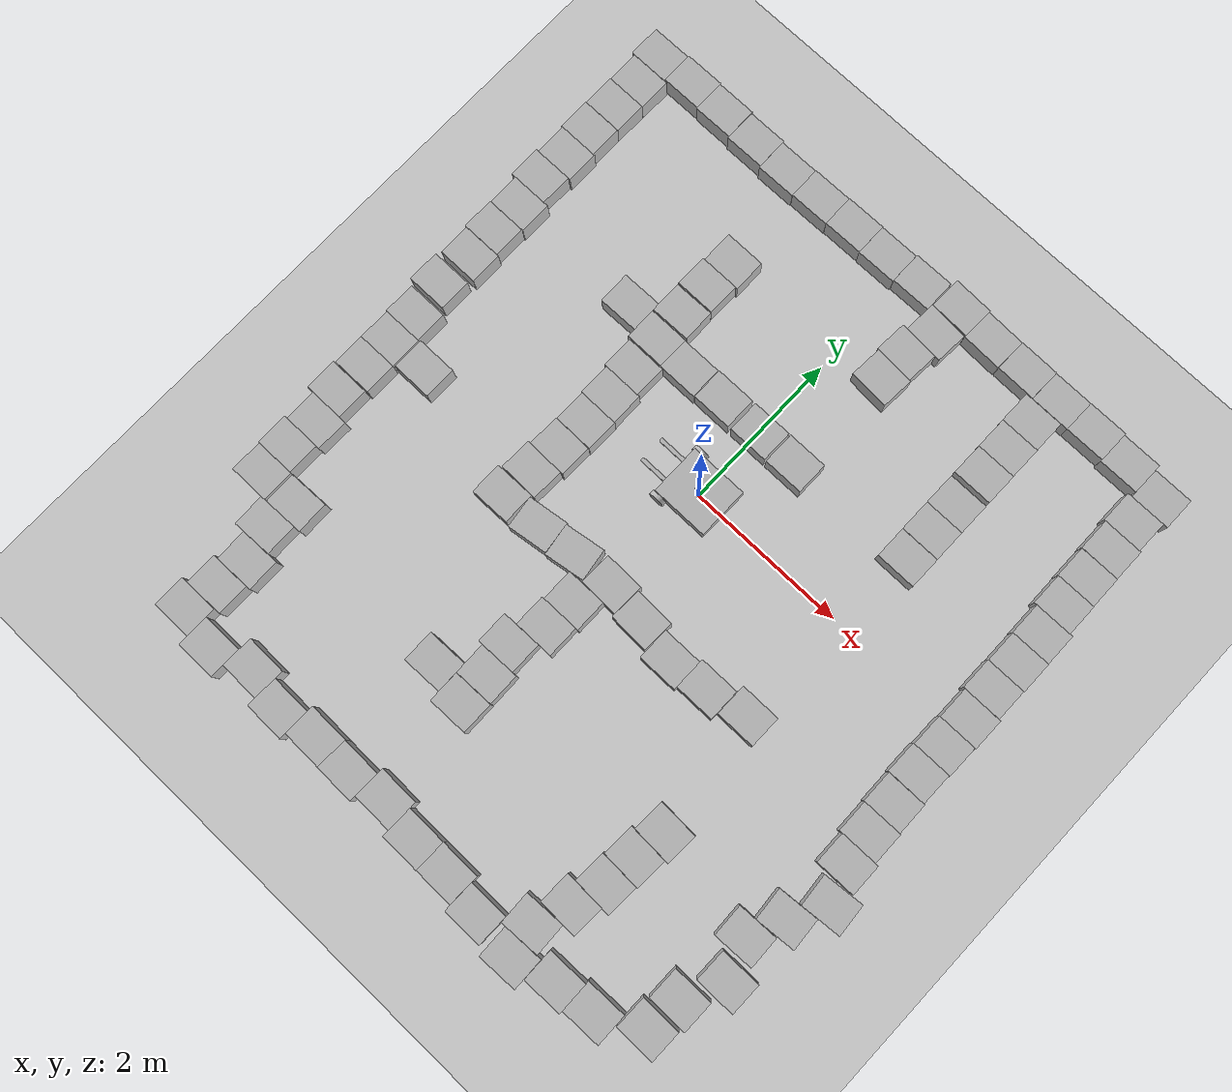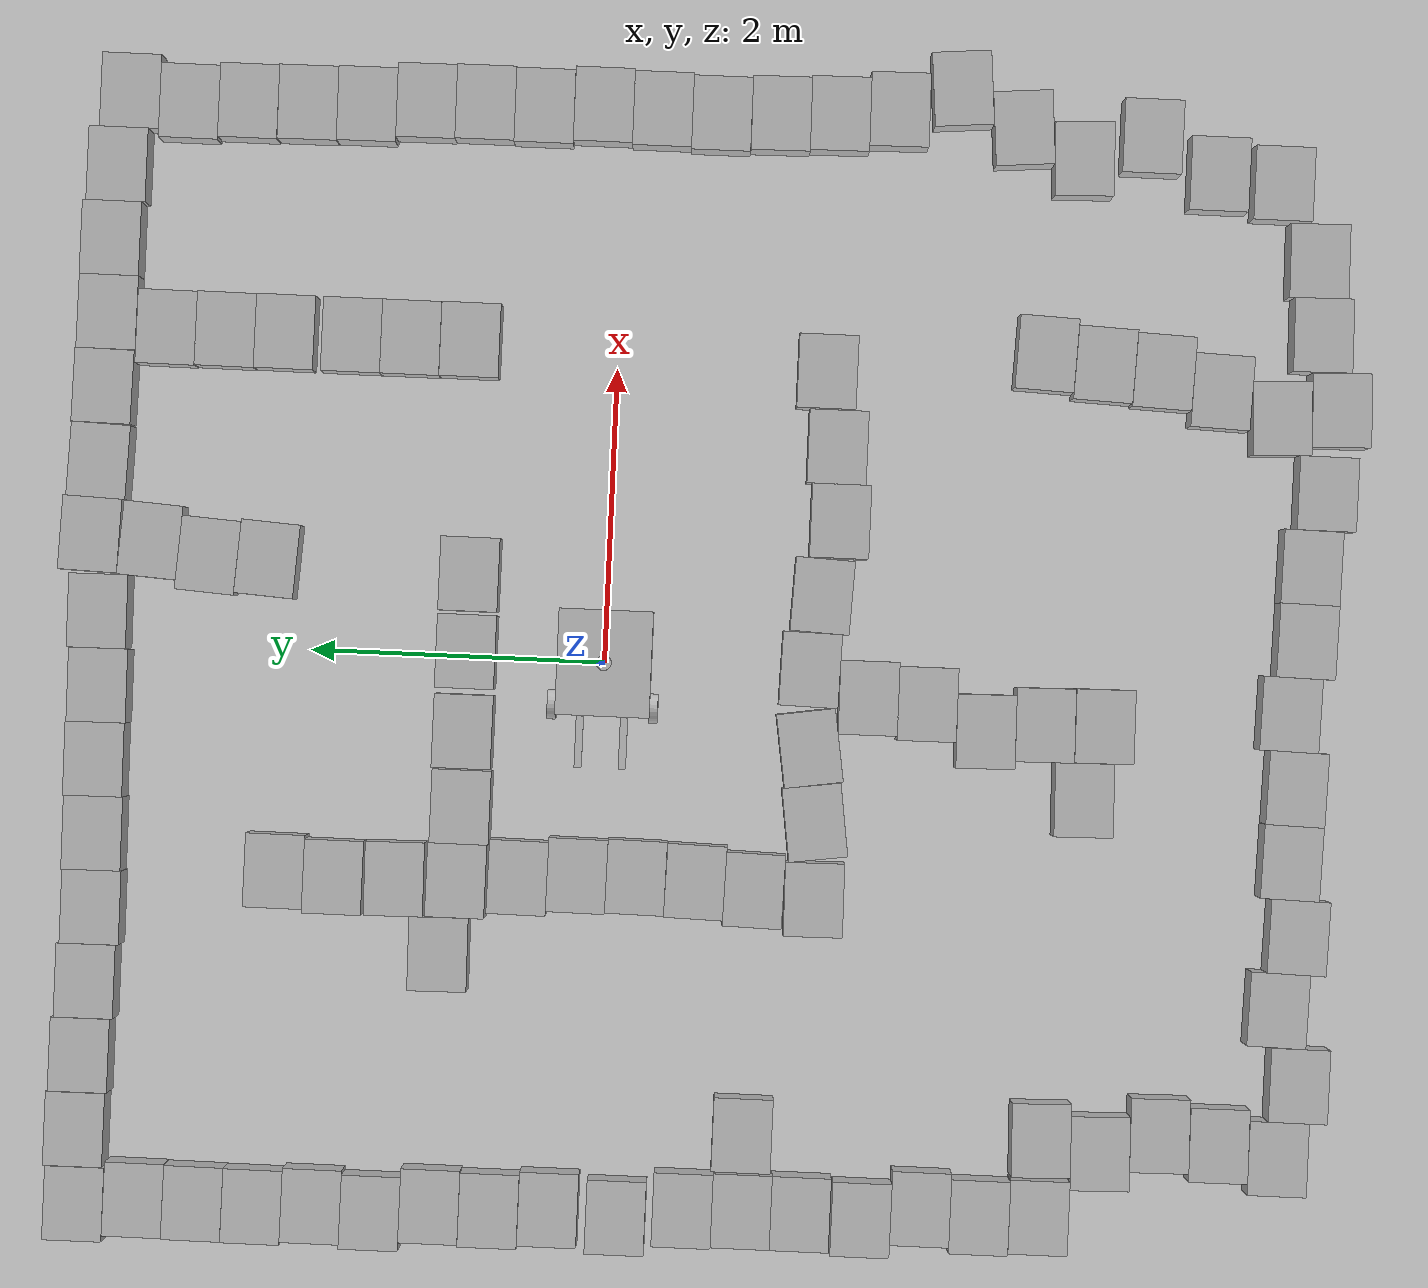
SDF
<sdf version="1.7">
 <world name="default">
  <light name="sun" type="directional">
   <pose>0 0 10 0 -0 0</pose>
   <diffuse>0.8 0.8 0.8 1</diffuse>
   <specular>0.2 0.2 0.2 1</specular>
   <attenuation>
    <range>1000</range>
    <constant>0.9</constant>
    <linear>0.01</linear>
    <quadratic>0.001</quadratic>
   </attenuation>
   <direction>-0.5 0.1 -0.9</direction>
   <spot><inner_angle>0</inner_angle><outer_angle>0</outer_angle><falloff>0</falloff></spot>
  </light>
  <model name="ground_plane">
   <static>1</static>
   <link name="link">
    <collision name="collision">
     <geometry><plane><normal>0 0 1</normal><size>100 100</size></plane></geometry>
     <surface><friction><ode><mu>100</mu><mu2>50</mu2></ode></friction></surface>
    </collision>
    <visual name="visual">
     <cast_shadows>0</cast_shadows>
     <geometry><plane><normal>0 0 1</normal><size>100 100</size></plane></geometry>
     <material>
      <script><uri>file://media/materials/scripts/gazebo.material</uri><name>Gazebo/Grey</name></script>
     </material>
    </visual>
   </link>
  </model>
  <gravity>0 0 -9.8</gravity>
  <magnetic_field>6e-06 2.3e-05 -4.2e-05</magnetic_field>
  <atmosphere type="adiabatic"/>
  <physics type="ode">
   <max_step_size>0.001</max_step_size>
   <real_time_factor>1</real_time_factor>
   <real_time_update_rate>1000</real_time_update_rate>
  </physics>
  <scene><ambient>0.4 0.4 0.4 1</ambient><background>0.7 0.7 0.7 1</background><shadows>1</shadows></scene>
  <spherical_coordinates>
   <surface_model>EARTH_WGS84</surface_model>
   <latitude_deg>0</latitude_deg>
   <longitude_deg>0</longitude_deg>
   <elevation>0</elevation>
   <heading_deg>0</heading_deg>
  </spherical_coordinates>
  <model name="lgv">
   <link name="base_link">
    <inertial>
     <pose>0.006527 0 -0.002704 1.5708 -0 1.5708</pose>
     <mass>10.725</mass>
     <inertia>
      <ixx>0.476011</ixx>
      <ixy>1.73103e-18</ixy>
      <ixz>-2.64669e-18</ixz>
      <iyy>0.784563</iyy>
      <iyz>0.00611072</iyz>
      <izz>0.376002</izz>
     </inertia>
    </inertial>
    <collision name="base_link_collision"><geometry><box><size>0.72 0.64 0.18</size></box></geometry></collision>
    <collision name="base_link_fixed_joint_lump__front_caster_collision_1">
     <pose>0.14 0 -0.09 0 -0 0</pose>
     <geometry><sphere><radius>0.06</radius></sphere></geometry>
    </collision>
    <collision name="base_link_fixed_joint_lump__imu_link_collision_2">
     <pose>0 0 0.01 0 -0 0</pose>
     <geometry><box><size>0.1 0.1 0.1</size></box></geometry>
    </collision>
    <collision name="base_link_fixed_joint_lump__lidar_link_collision_3">
     <pose>0 0 0.12 0 -0 0</pose>
     <geometry><cylinder><length>0.055</length><radius>0.0508</radius></cylinder></geometry>
    </collision>
    <visual name="base_link_visual"><geometry><box><size>0.72 0.64 0.18</size></box></geometry></visual>
    <visual name="base_link_fixed_joint_lump__front_caster_visual_1">
     <pose>0.14 0 -0.09 0 -0 0</pose>
     <geometry><sphere><radius>0.06</radius></sphere></geometry>
    </visual>
    <visual name="base_link_fixed_joint_lump__dummyfork_l_link_visual_2">
     <pose>-0.54 0.15 0.01 0 -0 0</pose>
     <geometry><box><size>0.35 0.05 0.01</size></box></geometry>
    </visual>
    <visual name="base_link_fixed_joint_lump__dummyfork_r_link_visual_3">
     <pose>-0.54 -0.15 0.01 0 -0 0</pose>
     <geometry><box><size>0.35 0.05 0.01</size></box></geometry>
    </visual>
    <visual name="base_link_fixed_joint_lump__imu_link_visual_4">
     <pose>0 0 0.01 0 -0 0</pose>
     <geometry><box><size>0.1 0.1 0.1</size></box></geometry>
    </visual>
    <visual name="base_link_fixed_joint_lump__lidar_link_visual_5">
     <pose>0 0 0.12 0 -0 0</pose>
     <geometry><cylinder><length>0.055</length><radius>0.0508</radius></cylinder></geometry>
    </visual>
    <sensor name="imu_sensor" type="imu">
     <plugin name="imu_plugin" filename="libgazebo_ros_imu_sensor.so">
      <ros><remapping>~/out:=imu/data</remapping></ros>
      <initial_orientation_as_reference>0</initial_orientation_as_reference>
     </plugin>
     <always_on>1</always_on>
     <update_rate>100</update_rate>
     <visualize>1</visualize>
     <imu>
      <angular_velocity>
       <x>
        <noise type="gaussian">
         <mean>0</mean>
         <stddev>0.0002</stddev>
         <bias_mean>7.5e-06</bias_mean>
         <bias_stddev>8e-07</bias_stddev>
        </noise>
       </x>
       <y>
        <noise type="gaussian">
         <mean>0</mean>
         <stddev>0.0002</stddev>
         <bias_mean>7.5e-06</bias_mean>
         <bias_stddev>8e-07</bias_stddev>
        </noise>
       </y>
       <z>
        <noise type="gaussian">
         <mean>0</mean>
         <stddev>0.0002</stddev>
         <bias_mean>7.5e-06</bias_mean>
         <bias_stddev>8e-07</bias_stddev>
        </noise>
       </z>
      </angular_velocity>
      <linear_acceleration>
       <x>
        <noise type="gaussian">
         <mean>0</mean>
         <stddev>0.017</stddev>
         <bias_mean>0.1</bias_mean>
         <bias_stddev>0.001</bias_stddev>
        </noise>
       </x>
       <y>
        <noise type="gaussian">
         <mean>0</mean>
         <stddev>0.017</stddev>
         <bias_mean>0.1</bias_mean>
         <bias_stddev>0.001</bias_stddev>
        </noise>
       </y>
       <z>
        <noise type="gaussian">
         <mean>0</mean>
         <stddev>0.017</stddev>
         <bias_mean>0.1</bias_mean>
         <bias_stddev>0.001</bias_stddev>
        </noise>
       </z>
      </linear_acceleration>
     </imu>
     <pose>0 0 0.01 0 -0 0</pose>
    </sensor>
    <sensor name="lidar" type="ray">
     <always_on>1</always_on>
     <visualize>1</visualize>
     <update_rate>5</update_rate>
     <ray>
      <scan>
       <horizontal>
        <samples>360</samples>
        <resolution>1</resolution>
        <min_angle>0</min_angle>
        <max_angle>6.28</max_angle>
       </horizontal>
       <vertical><samples>1</samples><min_angle>0</min_angle><max_angle>0</max_angle></vertical>
      </scan>
      <range><min>0.12</min><max>3.5</max><resolution>0.015</resolution></range>
      <noise><type>gaussian</type><mean>0</mean><stddev>0.01</stddev></noise>
     </ray>
     <plugin name="scan" filename="libgazebo_ros_ray_sensor.so">
      <ros><remapping>~/out:=scan</remapping></ros>
      <output_type>sensor_msgs/LaserScan</output_type>
      <frame_name>lidar_link</frame_name>
     </plugin>
     <pose>0 0 0.12 0 -0 0</pose>
    </sensor>
   </link>
   <joint name="drivewhl_l_joint" type="revolute">
    <pose relative_to="base_link">-0.295 0.345 -0.05 0 -0 0</pose>
    <parent>base_link</parent>
    <child>drivewhl_l_link</child>
    <axis>
     <xyz>0 1 0</xyz>
     <limit><lower>-1e+16</lower><upper>1e+16</upper></limit>
     <dynamics><spring_reference>0</spring_reference><spring_stiffness>0</spring_stiffness></dynamics>
    </axis>
   </joint>
   <link name="drivewhl_l_link">
    <pose relative_to="drivewhl_l_joint">0 0 0 0 -0 0</pose>
    <inertial>
     <pose>0 0 0 1.5708 -0 0</pose>
     <mass>5</mass>
     <inertia><ixx>0.014</ixx><ixy>0</ixy><ixz>0</ixz><iyy>0.014</iyy><iyz>0</iyz><izz>0.025</izz></inertia>
    </inertial>
    <collision name="drivewhl_l_link_collision">
     <pose>0 0 0 1.5708 -0 0</pose>
     <geometry><cylinder><length>0.06</length><radius>0.1</radius></cylinder></geometry>
    </collision>
    <visual name="drivewhl_l_link_visual">
     <pose>0 0 0 1.5708 -0 0</pose>
     <geometry><cylinder><length>0.06</length><radius>0.1</radius></cylinder></geometry>
    </visual>
   </link>
   <joint name="drivewhl_r_joint" type="revolute">
    <pose relative_to="base_link">-0.295 -0.345 -0.05 0 -0 0</pose>
    <parent>base_link</parent>
    <child>drivewhl_r_link</child>
    <axis>
     <xyz>0 1 0</xyz>
     <limit><lower>-1e+16</lower><upper>1e+16</upper></limit>
     <dynamics><spring_reference>0</spring_reference><spring_stiffness>0</spring_stiffness></dynamics>
    </axis>
   </joint>
   <link name="drivewhl_r_link">
    <pose relative_to="drivewhl_r_joint">0 0 0 0 -0 0</pose>
    <inertial>
     <pose>0 0 0 1.5708 -0 0</pose>
     <mass>5</mass>
     <inertia><ixx>0.014</ixx><ixy>0</ixy><ixz>0</ixz><iyy>0.014</iyy><iyz>0</iyz><izz>0.025</izz></inertia>
    </inertial>
    <collision name="drivewhl_r_link_collision">
     <pose>0 0 0 1.5708 -0 0</pose>
     <geometry><cylinder><length>0.06</length><radius>0.1</radius></cylinder></geometry>
    </collision>
    <visual name="drivewhl_r_link_visual">
     <pose>0 0 0 1.5708 -0 0</pose>
     <geometry><cylinder><length>0.06</length><radius>0.1</radius></cylinder></geometry>
    </visual>
   </link>
   <static>0</static>
   <plugin name="Plugin_diff_drive" filename="libgazebo_ros_diff_drive.so">
    <update_rate>30</update_rate>
    <command_topic>cmd_vel</command_topic>
    <left_joint>drivewhl_l_joint</left_joint>
    <right_joint>drivewhl_r_joint</right_joint>
    <wheel_separation>0.75</wheel_separation>
    <wheel_diameter>0.2</wheel_diameter>
    <max_wheel_torque>100</max_wheel_torque>
    <max_wheel_acceleration>1.5</max_wheel_acceleration>
    <publish_odom>1</publish_odom>
    <publish_odom_tf>0</publish_odom_tf>
    <publish_wheel_tf>0</publish_wheel_tf>
    <odometry_topic>odom</odometry_topic>
    <odometry_frame>odom</odometry_frame>
    <robot_base_frame>base_link</robot_base_frame>
    <odometry_source>1</odometry_source>
    <ros><remapping>odom:=wheel/odometry</remapping></ros>
   </plugin>
   <plugin name="Plugin_joint_state_publisher" filename="libgazebo_ros_joint_state_publisher.so">
    <ros><remapping>~/out:=joint_states</remapping></ros>
    <update_rate>30</update_rate>
    <joint_name>drivewhl_l_joint</joint_name>
    <joint_name>drivewhl_r_joint</joint_name>
   </plugin>
   <pose>-5.2e-05 9e-05 0.15 0 -0 0.001111</pose>
  </model>
  <model name="cardboard_box">
   <pose>-0.504733 0.934139 0.149 0 -0 0</pose>
   <link name="link">
    <inertial>
     <mass>2</mass>
     <inertia>
      <ixx>0.0416667</ixx>
      <ixy>0</ixy>
      <ixz>0</ixz>
      <iyy>0.0566667</iyy>
      <iyz>0</iyz>
      <izz>0.0683333</izz>
     </inertia>
    </inertial>
    <collision name="collision">
     <geometry><box><size>0.5 0.4 0.3</size></box></geometry>
     <surface>
      <friction><ode><mu>1</mu><mu2>1</mu2></ode></friction>
      <contact><ode><kp>1e+07</kp><kd>1</kd><min_depth>0.001</min_depth><max_vel>0.1</max_vel></ode></contact>
     </surface>
    </collision>
    <visual name="visual">
     <pose>0 0 -0.15 0 -0 0</pose>
     <geometry>
      <mesh><uri>model://cardboard_box/meshes/cardboard_box.dae</uri><scale>1.25932 1.00745 0.755591</scale></mesh>
     </geometry>
    </visual>
   </link>
  </model>
  <model name="cardboard_box_clone">
   <pose>0.036399 0.936347 0.149 0 -0 0</pose>
   <link name="link">
    <inertial>
     <mass>2</mass>
     <inertia>
      <ixx>0.0416667</ixx>
      <ixy>0</ixy>
      <ixz>0</ixz>
      <iyy>0.0566667</iyy>
      <iyz>0</iyz>
      <izz>0.0683333</izz>
     </inertia>
    </inertial>
    <collision name="collision">
     <geometry><box><size>0.5 0.4 0.3</size></box></geometry>
     <surface>
      <friction><ode><mu>1</mu><mu2>1</mu2></ode></friction>
      <contact><ode><kp>1e+07</kp><kd>1</kd><min_depth>0.001</min_depth><max_vel>0.1</max_vel></ode></contact>
     </surface>
    </collision>
    <visual name="visual">
     <pose>0 0 -0.15 0 -0 0</pose>
     <geometry>
      <mesh><uri>model://cardboard_box/meshes/cardboard_box.dae</uri><scale>1.25932 1.00745 0.755591</scale></mesh>
     </geometry>
    </visual>
   </link>
  </model>
  <model name="cardboard_box_clone_0">
   <pose>0.559122 0.936933 0.149 0 -0 0</pose>
   <link name="link">
    <inertial>
     <mass>2</mass>
     <inertia>
      <ixx>0.0416667</ixx>
      <ixy>0</ixy>
      <ixz>0</ixz>
      <iyy>0.0566667</iyy>
      <iyz>0</iyz>
      <izz>0.0683333</izz>
     </inertia>
    </inertial>
    <collision name="collision">
     <geometry><box><size>0.5 0.4 0.3</size></box></geometry>
     <surface>
      <friction><ode><mu>1</mu><mu2>1</mu2></ode></friction>
      <contact><ode><kp>1e+07</kp><kd>1</kd><min_depth>0.001</min_depth><max_vel>0.1</max_vel></ode></contact>
     </surface>
    </collision>
    <visual name="visual">
     <pose>0 0 -0.15 0 -0 0</pose>
     <geometry>
      <mesh><uri>model://cardboard_box/meshes/cardboard_box.dae</uri><scale>1.25932 1.00745 0.755591</scale></mesh>
     </geometry>
    </visual>
   </link>
  </model>
  <model name="cardboard_box_clone_1">
   <pose>-1.0138 0.925384 0.149 0 -0 0.00015</pose>
   <link name="link">
    <inertial>
     <mass>2</mass>
     <inertia>
      <ixx>0.0416667</ixx>
      <ixy>0</ixy>
      <ixz>0</ixz>
      <iyy>0.0566667</iyy>
      <iyz>0</iyz>
      <izz>0.0683333</izz>
     </inertia>
    </inertial>
    <collision name="collision">
     <geometry><box><size>0.5 0.4 0.3</size></box></geometry>
     <surface>
      <friction><ode><mu>1</mu><mu2>1</mu2></ode></friction>
      <contact><ode><kp>1e+07</kp><kd>1</kd><min_depth>0.001</min_depth><max_vel>0.1</max_vel></ode></contact>
     </surface>
    </collision>
    <visual name="visual">
     <pose>0 0 -0.15 0 -0 0</pose>
     <geometry>
      <mesh><uri>model://cardboard_box/meshes/cardboard_box.dae</uri><scale>1.25932 1.00745 0.755591</scale></mesh>
     </geometry>
    </visual>
   </link>
  </model>
  <model name="cardboard_box_clone_2">
   <pose>-1.51293 0.932592 0.149 0 -0 0.000262</pose>
   <link name="link">
    <inertial>
     <mass>2</mass>
     <inertia>
      <ixx>0.0416667</ixx>
      <ixy>0</ixy>
      <ixz>0</ixz>
      <iyy>0.0566667</iyy>
      <iyz>0</iyz>
      <izz>0.0683333</izz>
     </inertia>
    </inertial>
    <collision name="collision">
     <geometry><box><size>0.5 0.4 0.3</size></box></geometry>
     <surface>
      <friction><ode><mu>1</mu><mu2>1</mu2></ode></friction>
      <contact><ode><kp>1e+07</kp><kd>1</kd><min_depth>0.001</min_depth><max_vel>0.1</max_vel></ode></contact>
     </surface>
    </collision>
    <visual name="visual">
     <pose>0 0 -0.15 0 -0 0</pose>
     <geometry>
      <mesh><uri>model://cardboard_box/meshes/cardboard_box.dae</uri><scale>1.25932 1.00745 0.755591</scale></mesh>
     </geometry>
    </visual>
   </link>
  </model>
  <model name="cardboard_box_clone_3">
   <pose>-1.47374 0.517825 0.149 0 0 -0.007011</pose>
   <link name="link">
    <inertial>
     <mass>2</mass>
     <inertia>
      <ixx>0.0416667</ixx>
      <ixy>0</ixy>
      <ixz>0</ixz>
      <iyy>0.0566667</iyy>
      <iyz>0</iyz>
      <izz>0.0683333</izz>
     </inertia>
    </inertial>
    <collision name="collision">
     <geometry><box><size>0.5 0.4 0.3</size></box></geometry>
     <surface>
      <friction><ode><mu>1</mu><mu2>1</mu2></ode></friction>
      <contact><ode><kp>1e+07</kp><kd>1</kd><min_depth>0.001</min_depth><max_vel>0.1</max_vel></ode></contact>
     </surface>
    </collision>
    <visual name="visual">
     <pose>0 0 -0.15 0 -0 0</pose>
     <geometry>
      <mesh><uri>model://cardboard_box/meshes/cardboard_box.dae</uri><scale>1.25932 1.00745 0.755591</scale></mesh>
     </geometry>
    </visual>
   </link>
  </model>
  <model name="cardboard_box_clone_4">
   <pose>-1.44358 0.118344 0.149 0 0 -0.006992</pose>
   <link name="link">
    <inertial>
     <mass>2</mass>
     <inertia>
      <ixx>0.0416667</ixx>
      <ixy>0</ixy>
      <ixz>0</ixz>
      <iyy>0.0566667</iyy>
      <iyz>0</iyz>
      <izz>0.0683333</izz>
     </inertia>
    </inertial>
    <collision name="collision">
     <geometry><box><size>0.5 0.4 0.3</size></box></geometry>
     <surface>
      <friction><ode><mu>1</mu><mu2>1</mu2></ode></friction>
      <contact><ode><kp>1e+07</kp><kd>1</kd><min_depth>0.001</min_depth><max_vel>0.1</max_vel></ode></contact>
     </surface>
    </collision>
    <visual name="visual">
     <pose>0 0 -0.15 0 -0 0</pose>
     <geometry>
      <mesh><uri>model://cardboard_box/meshes/cardboard_box.dae</uri><scale>1.25932 1.00745 0.755591</scale></mesh>
     </geometry>
    </visual>
   </link>
  </model>
  <model name="cardboard_box_clone_5">
   <pose>-1.43679 -0.281524 0.149 -0 -0 -0.009797</pose>
   <link name="link">
    <inertial>
     <mass>2</mass>
     <inertia>
      <ixx>0.0416667</ixx>
      <ixy>0</ixy>
      <ixz>0</ixz>
      <iyy>0.0566667</iyy>
      <iyz>0</iyz>
      <izz>0.0683333</izz>
     </inertia>
    </inertial>
    <collision name="collision">
     <geometry><box><size>0.5 0.4 0.3</size></box></geometry>
     <surface>
      <friction><ode><mu>1</mu><mu2>1</mu2></ode></friction>
      <contact><ode><kp>1e+07</kp><kd>1</kd><min_depth>0.001</min_depth><max_vel>0.1</max_vel></ode></contact>
     </surface>
    </collision>
    <visual name="visual">
     <pose>0 0 -0.15 0 -0 0</pose>
     <geometry>
      <mesh><uri>model://cardboard_box/meshes/cardboard_box.dae</uri><scale>1.25932 1.00745 0.755591</scale></mesh>
     </geometry>
    </visual>
   </link>
  </model>
  <model name="cardboard_box_clone_6">
   <pose>-1.44817 -0.682981 0.149 0 -0 -0.019821</pose>
   <link name="link">
    <inertial>
     <mass>2</mass>
     <inertia>
      <ixx>0.0416667</ixx>
      <ixy>0</ixy>
      <ixz>0</ixz>
      <iyy>0.0566667</iyy>
      <iyz>0</iyz>
      <izz>0.0683333</izz>
     </inertia>
    </inertial>
    <collision name="collision">
     <geometry><box><size>0.5 0.4 0.3</size></box></geometry>
     <surface>
      <friction><ode><mu>1</mu><mu2>1</mu2></ode></friction>
      <contact><ode><kp>1e+07</kp><kd>1</kd><min_depth>0.001</min_depth><max_vel>0.1</max_vel></ode></contact>
     </surface>
    </collision>
    <visual name="visual">
     <pose>0 0 -0.15 0 -0 0</pose>
     <geometry>
      <mesh><uri>model://cardboard_box/meshes/cardboard_box.dae</uri><scale>1.25932 1.00745 0.755591</scale></mesh>
     </geometry>
    </visual>
   </link>
  </model>
  <model name="cardboard_box_clone_7">
   <pose>-1.48877 -1.08128 0.149 -0 -0 -0.019893</pose>
   <link name="link">
    <inertial>
     <mass>2</mass>
     <inertia>
      <ixx>0.0416667</ixx>
      <ixy>0</ixy>
      <ixz>0</ixz>
      <iyy>0.0566667</iyy>
      <iyz>0</iyz>
      <izz>0.0683333</izz>
     </inertia>
    </inertial>
    <collision name="collision">
     <geometry><box><size>0.5 0.4 0.3</size></box></geometry>
     <surface>
      <friction><ode><mu>1</mu><mu2>1</mu2></ode></friction>
      <contact><ode><kp>1e+07</kp><kd>1</kd><min_depth>0.001</min_depth><max_vel>0.1</max_vel></ode></contact>
     </surface>
    </collision>
    <visual name="visual">
     <pose>0 0 -0.15 0 -0 0</pose>
     <geometry>
      <mesh><uri>model://cardboard_box/meshes/cardboard_box.dae</uri><scale>1.25932 1.00745 0.755591</scale></mesh>
     </geometry>
    </visual>
   </link>
  </model>
  <model name="cardboard_box_clone_8">
   <pose>-1.53394 -1.48869 0.149 0 -0 0.012453</pose>
   <link name="link">
    <inertial>
     <mass>2</mass>
     <inertia>
      <ixx>0.0416667</ixx>
      <ixy>0</ixy>
      <ixz>0</ixz>
      <iyy>0.0566667</iyy>
      <iyz>0</iyz>
      <izz>0.0683333</izz>
     </inertia>
    </inertial>
    <collision name="collision">
     <geometry><box><size>0.5 0.4 0.3</size></box></geometry>
     <surface>
      <friction><ode><mu>1</mu><mu2>1</mu2></ode></friction>
      <contact><ode><kp>1e+07</kp><kd>1</kd><min_depth>0.001</min_depth><max_vel>0.1</max_vel></ode></contact>
     </surface>
    </collision>
    <visual name="visual">
     <pose>0 0 -0.15 0 -0 0</pose>
     <geometry>
      <mesh><uri>model://cardboard_box/meshes/cardboard_box.dae</uri><scale>1.25932 1.00745 0.755591</scale></mesh>
     </geometry>
    </visual>
   </link>
  </model>
  <model name="cardboard_box_clone_9">
   <pose>-1.01175 -1.47132 0.149 0 -0 0.13741</pose>
   <link name="link">
    <inertial>
     <mass>2</mass>
     <inertia>
      <ixx>0.0416667</ixx>
      <ixy>0</ixy>
      <ixz>0</ixz>
      <iyy>0.0566667</iyy>
      <iyz>0</iyz>
      <izz>0.0683333</izz>
     </inertia>
    </inertial>
    <collision name="collision">
     <geometry><box><size>0.5 0.4 0.3</size></box></geometry>
     <surface>
      <friction><ode><mu>1</mu><mu2>1</mu2></ode></friction>
      <contact><ode><kp>1e+07</kp><kd>1</kd><min_depth>0.001</min_depth><max_vel>0.1</max_vel></ode></contact>
     </surface>
    </collision>
    <visual name="visual">
     <pose>0 0 -0.15 0 -0 0</pose>
     <geometry>
      <mesh><uri>model://cardboard_box/meshes/cardboard_box.dae</uri><scale>1.25932 1.00745 0.755591</scale></mesh>
     </geometry>
    </visual>
   </link>
  </model>
  <model name="cardboard_box_clone_10">
   <pose>-0.512427 -1.41527 0.149 0 -0 0.152729</pose>
   <link name="link">
    <inertial>
     <mass>2</mass>
     <inertia>
      <ixx>0.0416667</ixx>
      <ixy>0</ixy>
      <ixz>0</ixz>
      <iyy>0.0566667</iyy>
      <iyz>0</iyz>
      <izz>0.0683333</izz>
     </inertia>
    </inertial>
    <collision name="collision">
     <geometry><box><size>0.5 0.4 0.3</size></box></geometry>
     <surface>
      <friction><ode><mu>1</mu><mu2>1</mu2></ode></friction>
      <contact><ode><kp>1e+07</kp><kd>1</kd><min_depth>0.001</min_depth><max_vel>0.1</max_vel></ode></contact>
     </surface>
    </collision>
    <visual name="visual">
     <pose>0 0 -0.15 0 -0 0</pose>
     <geometry>
      <mesh><uri>model://cardboard_box/meshes/cardboard_box.dae</uri><scale>1.25932 1.00745 0.755591</scale></mesh>
     </geometry>
    </visual>
   </link>
  </model>
  <model name="cardboard_box_clone_11">
   <pose>0.018354 -1.39647 0.149 0 0 -0.020636</pose>
   <link name="link">
    <inertial>
     <mass>2</mass>
     <inertia>
      <ixx>0.0416667</ixx>
      <ixy>0</ixy>
      <ixz>0</ixz>
      <iyy>0.0566667</iyy>
      <iyz>0</iyz>
      <izz>0.0683333</izz>
     </inertia>
    </inertial>
    <collision name="collision">
     <geometry><box><size>0.5 0.4 0.3</size></box></geometry>
     <surface>
      <friction><ode><mu>1</mu><mu2>1</mu2></ode></friction>
      <contact><ode><kp>1e+07</kp><kd>1</kd><min_depth>0.001</min_depth><max_vel>0.1</max_vel></ode></contact>
     </surface>
    </collision>
    <visual name="visual">
     <pose>0 0 -0.15 0 -0 0</pose>
     <geometry>
      <mesh><uri>model://cardboard_box/meshes/cardboard_box.dae</uri><scale>1.25932 1.00745 0.755591</scale></mesh>
     </geometry>
    </visual>
   </link>
  </model>
  <model name="cardboard_box_clone_12">
   <pose>0.520326 -1.45543 0.149 0 -0 -0.043511</pose>
   <link name="link">
    <inertial>
     <mass>2</mass>
     <inertia>
      <ixx>0.0416667</ixx>
      <ixy>0</ixy>
      <ixz>0</ixz>
      <iyy>0.0566667</iyy>
      <iyz>0</iyz>
      <izz>0.0683333</izz>
     </inertia>
    </inertial>
    <collision name="collision">
     <geometry><box><size>0.5 0.4 0.3</size></box></geometry>
     <surface>
      <friction><ode><mu>1</mu><mu2>1</mu2></ode></friction>
      <contact><ode><kp>1e+07</kp><kd>1</kd><min_depth>0.001</min_depth><max_vel>0.1</max_vel></ode></contact>
     </surface>
    </collision>
    <visual name="visual">
     <pose>0 0 -0.15 0 -0 0</pose>
     <geometry>
      <mesh><uri>model://cardboard_box/meshes/cardboard_box.dae</uri><scale>1.25932 1.00745 0.755591</scale></mesh>
     </geometry>
    </visual>
   </link>
  </model>
  <model name="cardboard_box_clone_13">
   <pose>3.77819 -1.43207 0.149 0 -0 0.012439</pose>
   <link name="link">
    <inertial>
     <mass>2</mass>
     <inertia>
      <ixx>0.0416667</ixx>
      <ixy>0</ixy>
      <ixz>0</ixz>
      <iyy>0.0566667</iyy>
      <iyz>0</iyz>
      <izz>0.0683333</izz>
     </inertia>
    </inertial>
    <collision name="collision">
     <geometry><box><size>0.5 0.4 0.3</size></box></geometry>
     <surface>
      <friction><ode><mu>1</mu><mu2>1</mu2></ode></friction>
      <contact><ode><kp>1e+07</kp><kd>1</kd><min_depth>0.001</min_depth><max_vel>0.1</max_vel></ode></contact>
     </surface>
    </collision>
    <visual name="visual">
     <pose>0 0 -0.15 0 -0 0</pose>
     <geometry>
      <mesh><uri>model://cardboard_box/meshes/cardboard_box.dae</uri><scale>1.25932 1.00745 0.755591</scale></mesh>
     </geometry>
    </visual>
   </link>
  </model>
  <model name="cardboard_box_clone_14">
   <pose>3.76152 -1.03289 0.149 0 -0 0.012281</pose>
   <link name="link">
    <inertial>
     <mass>2</mass>
     <inertia>
      <ixx>0.0416667</ixx>
      <ixy>0</ixy>
      <ixz>0</ixz>
      <iyy>0.0566667</iyy>
      <iyz>0</iyz>
      <izz>0.0683333</izz>
     </inertia>
    </inertial>
    <collision name="collision">
     <geometry><box><size>0.5 0.4 0.3</size></box></geometry>
     <surface>
      <friction><ode><mu>1</mu><mu2>1</mu2></ode></friction>
      <contact><ode><kp>1e+07</kp><kd>1</kd><min_depth>0.001</min_depth><max_vel>0.1</max_vel></ode></contact>
     </surface>
    </collision>
    <visual name="visual">
     <pose>0 0 -0.15 0 -0 0</pose>
     <geometry>
      <mesh><uri>model://cardboard_box/meshes/cardboard_box.dae</uri><scale>1.25932 1.00745 0.755591</scale></mesh>
     </geometry>
    </visual>
   </link>
  </model>
  <model name="cardboard_box_clone_15">
   <pose>3.74406 -0.631957 0.149 0 -0 0.004283</pose>
   <link name="link">
    <inertial>
     <mass>2</mass>
     <inertia>
      <ixx>0.0416667</ixx>
      <ixy>0</ixy>
      <ixz>0</ixz>
      <iyy>0.0566667</iyy>
      <iyz>0</iyz>
      <izz>0.0683333</izz>
     </inertia>
    </inertial>
    <collision name="collision">
     <geometry><box><size>0.5 0.4 0.3</size></box></geometry>
     <surface>
      <friction><ode><mu>1</mu><mu2>1</mu2></ode></friction>
      <contact><ode><kp>1e+07</kp><kd>1</kd><min_depth>0.001</min_depth><max_vel>0.1</max_vel></ode></contact>
     </surface>
    </collision>
    <visual name="visual">
     <pose>0 0 -0.15 0 -0 0</pose>
     <geometry>
      <mesh><uri>model://cardboard_box/meshes/cardboard_box.dae</uri><scale>1.25932 1.00745 0.755591</scale></mesh>
     </geometry>
    </visual>
   </link>
  </model>
  <model name="cardboard_box_clone_16">
   <pose>3.75626 -0.232679 0.149 0 -0 0.004095</pose>
   <link name="link">
    <inertial>
     <mass>2</mass>
     <inertia>
      <ixx>0.0416667</ixx>
      <ixy>0</ixy>
      <ixz>0</ixz>
      <iyy>0.0566667</iyy>
      <iyz>0</iyz>
      <izz>0.0683333</izz>
     </inertia>
    </inertial>
    <collision name="collision">
     <geometry><box><size>0.5 0.4 0.3</size></box></geometry>
     <surface>
      <friction><ode><mu>1</mu><mu2>1</mu2></ode></friction>
      <contact><ode><kp>1e+07</kp><kd>1</kd><min_depth>0.001</min_depth><max_vel>0.1</max_vel></ode></contact>
     </surface>
    </collision>
    <visual name="visual">
     <pose>0 0 -0.15 0 -0 0</pose>
     <geometry>
      <mesh><uri>model://cardboard_box/meshes/cardboard_box.dae</uri><scale>1.25932 1.00745 0.755591</scale></mesh>
     </geometry>
    </visual>
   </link>
  </model>
  <model name="cardboard_box_clone_17">
   <pose>3.76732 0.166908 0.149 0 -0 0.002251</pose>
   <link name="link">
    <inertial>
     <mass>2</mass>
     <inertia>
      <ixx>0.0416667</ixx>
      <ixy>0</ixy>
      <ixz>0</ixz>
      <iyy>0.0566667</iyy>
      <iyz>0</iyz>
      <izz>0.0683333</izz>
     </inertia>
    </inertial>
    <collision name="collision">
     <geometry><box><size>0.5 0.4 0.3</size></box></geometry>
     <surface>
      <friction><ode><mu>1</mu><mu2>1</mu2></ode></friction>
      <contact><ode><kp>1e+07</kp><kd>1</kd><min_depth>0.001</min_depth><max_vel>0.1</max_vel></ode></contact>
     </surface>
    </collision>
    <visual name="visual">
     <pose>0 0 -0.15 0 -0 0</pose>
     <geometry>
      <mesh><uri>model://cardboard_box/meshes/cardboard_box.dae</uri><scale>1.25932 1.00745 0.755591</scale></mesh>
     </geometry>
    </visual>
   </link>
  </model>
  <model name="cardboard_box_clone_18">
   <pose>3.74224 0.567245 0.149 0 -0 0.004212</pose>
   <link name="link">
    <inertial>
     <mass>2</mass>
     <inertia>
      <ixx>0.0416667</ixx>
      <ixy>0</ixy>
      <ixz>0</ixz>
      <iyy>0.0566667</iyy>
      <iyz>0</iyz>
      <izz>0.0683333</izz>
     </inertia>
    </inertial>
    <collision name="collision">
     <geometry><box><size>0.5 0.4 0.3</size></box></geometry>
     <surface>
      <friction><ode><mu>1</mu><mu2>1</mu2></ode></friction>
      <contact><ode><kp>1e+07</kp><kd>1</kd><min_depth>0.001</min_depth><max_vel>0.1</max_vel></ode></contact>
     </surface>
    </collision>
    <visual name="visual">
     <pose>0 0 -0.15 0 -0 0</pose>
     <geometry>
      <mesh><uri>model://cardboard_box/meshes/cardboard_box.dae</uri><scale>1.25932 1.00745 0.755591</scale></mesh>
     </geometry>
    </visual>
   </link>
  </model>
  <model name="cardboard_box_clone_19">
   <pose>3.74645 0.967047 0.149 0 -0 0.005082</pose>
   <link name="link">
    <inertial>
     <mass>2</mass>
     <inertia>
      <ixx>0.0416667</ixx>
      <ixy>0</ixy>
      <ixz>0</ixz>
      <iyy>0.0566667</iyy>
      <iyz>0</iyz>
      <izz>0.0683333</izz>
     </inertia>
    </inertial>
    <collision name="collision">
     <geometry><box><size>0.5 0.4 0.3</size></box></geometry>
     <surface>
      <friction><ode><mu>1</mu><mu2>1</mu2></ode></friction>
      <contact><ode><kp>1e+07</kp><kd>1</kd><min_depth>0.001</min_depth><max_vel>0.1</max_vel></ode></contact>
     </surface>
    </collision>
    <visual name="visual">
     <pose>0 0 -0.15 0 -0 0</pose>
     <geometry>
      <mesh><uri>model://cardboard_box/meshes/cardboard_box.dae</uri><scale>1.25932 1.00745 0.755591</scale></mesh>
     </geometry>
    </visual>
   </link>
  </model>
  <model name="cardboard_box_clone_20">
   <pose>3.73943 1.36651 0.149 0 -0 0.006875</pose>
   <link name="link">
    <inertial>
     <mass>2</mass>
     <inertia>
      <ixx>0.0416667</ixx>
      <ixy>0</ixy>
      <ixz>0</ixz>
      <iyy>0.0566667</iyy>
      <iyz>0</iyz>
      <izz>0.0683333</izz>
     </inertia>
    </inertial>
    <collision name="collision">
     <geometry><box><size>0.5 0.4 0.3</size></box></geometry>
     <surface>
      <friction><ode><mu>1</mu><mu2>1</mu2></ode></friction>
      <contact><ode><kp>1e+07</kp><kd>1</kd><min_depth>0.001</min_depth><max_vel>0.1</max_vel></ode></contact>
     </surface>
    </collision>
    <visual name="visual">
     <pose>0 0 -0.15 0 -0 0</pose>
     <geometry>
      <mesh><uri>model://cardboard_box/meshes/cardboard_box.dae</uri><scale>1.25932 1.00745 0.755591</scale></mesh>
     </geometry>
    </visual>
   </link>
  </model>
  <model name="cardboard_box_clone_21">
   <pose>2.14051 1.00085 0.149 0 -0 0</pose>
   <link name="link">
    <inertial>
     <mass>2</mass>
     <inertia>
      <ixx>0.0416667</ixx>
      <ixy>0</ixy>
      <ixz>0</ixz>
      <iyy>0.0566667</iyy>
      <iyz>0</iyz>
      <izz>0.0683333</izz>
     </inertia>
    </inertial>
    <collision name="collision">
     <geometry><box><size>0.5 0.4 0.3</size></box></geometry>
     <surface>
      <friction><ode><mu>1</mu><mu2>1</mu2></ode></friction>
      <contact><ode><kp>1e+07</kp><kd>1</kd><min_depth>0.001</min_depth><max_vel>0.1</max_vel></ode></contact>
     </surface>
    </collision>
    <visual name="visual">
     <pose>0 0 -0.15 0 -0 0</pose>
     <geometry>
      <mesh><uri>model://cardboard_box/meshes/cardboard_box.dae</uri><scale>1.25932 1.00745 0.755591</scale></mesh>
     </geometry>
    </visual>
   </link>
  </model>
  <model name="cardboard_box_clone_22">
   <pose>2.13804 1.4019 0.149 0 -0 0</pose>
   <link name="link">
    <inertial>
     <mass>2</mass>
     <inertia>
      <ixx>0.0416667</ixx>
      <ixy>0</ixy>
      <ixz>0</ixz>
      <iyy>0.0566667</iyy>
      <iyz>0</iyz>
      <izz>0.0683333</izz>
     </inertia>
    </inertial>
    <collision name="collision">
     <geometry><box><size>0.5 0.4 0.3</size></box></geometry>
     <surface>
      <friction><ode><mu>1</mu><mu2>1</mu2></ode></friction>
      <contact><ode><kp>1e+07</kp><kd>1</kd><min_depth>0.001</min_depth><max_vel>0.1</max_vel></ode></contact>
     </surface>
    </collision>
    <visual name="visual">
     <pose>0 0 -0.15 0 -0 0</pose>
     <geometry>
      <mesh><uri>model://cardboard_box/meshes/cardboard_box.dae</uri><scale>1.25932 1.00745 0.755591</scale></mesh>
     </geometry>
    </visual>
   </link>
  </model>
  <model name="cardboard_box_clone_23">
   <pose>2.13738 1.80107 0.149 0 -0 2e-06</pose>
   <link name="link">
    <inertial>
     <mass>2</mass>
     <inertia>
      <ixx>0.0416667</ixx>
      <ixy>0</ixy>
      <ixz>0</ixz>
      <iyy>0.0566667</iyy>
      <iyz>0</iyz>
      <izz>0.0683333</izz>
     </inertia>
    </inertial>
    <collision name="collision">
     <geometry><box><size>0.5 0.4 0.3</size></box></geometry>
     <surface>
      <friction><ode><mu>1</mu><mu2>1</mu2></ode></friction>
      <contact><ode><kp>1e+07</kp><kd>1</kd><min_depth>0.001</min_depth><max_vel>0.1</max_vel></ode></contact>
     </surface>
    </collision>
    <visual name="visual">
     <pose>0 0 -0.15 0 -0 0</pose>
     <geometry>
      <mesh><uri>model://cardboard_box/meshes/cardboard_box.dae</uri><scale>1.25932 1.00745 0.755591</scale></mesh>
     </geometry>
    </visual>
   </link>
  </model>
  <model name="cardboard_box_clone_24">
   <pose>2.13776 2.25388 0.149 -0 -0 -0.003863</pose>
   <link name="link">
    <inertial>
     <mass>2</mass>
     <inertia>
      <ixx>0.0416667</ixx>
      <ixy>0</ixy>
      <ixz>0</ixz>
      <iyy>0.0566667</iyy>
      <iyz>0</iyz>
      <izz>0.0683333</izz>
     </inertia>
    </inertial>
    <collision name="collision">
     <geometry><box><size>0.5 0.4 0.3</size></box></geometry>
     <surface>
      <friction><ode><mu>1</mu><mu2>1</mu2></ode></friction>
      <contact><ode><kp>1e+07</kp><kd>1</kd><min_depth>0.001</min_depth><max_vel>0.1</max_vel></ode></contact>
     </surface>
    </collision>
    <visual name="visual">
     <pose>0 0 -0.15 0 -0 0</pose>
     <geometry>
      <mesh><uri>model://cardboard_box/meshes/cardboard_box.dae</uri><scale>1.25932 1.00745 0.755591</scale></mesh>
     </geometry>
    </visual>
   </link>
  </model>
  <model name="cardboard_box_clone_25">
   <pose>2.13582 2.65368 0.149 0 -0 -0.004025</pose>
   <link name="link">
    <inertial>
     <mass>2</mass>
     <inertia>
      <ixx>0.0416667</ixx>
      <ixy>0</ixy>
      <ixz>0</ixz>
      <iyy>0.0566667</iyy>
      <iyz>0</iyz>
      <izz>0.0683333</izz>
     </inertia>
    </inertial>
    <collision name="collision">
     <geometry><box><size>0.5 0.4 0.3</size></box></geometry>
     <surface>
      <friction><ode><mu>1</mu><mu2>1</mu2></ode></friction>
      <contact><ode><kp>1e+07</kp><kd>1</kd><min_depth>0.001</min_depth><max_vel>0.1</max_vel></ode></contact>
     </surface>
    </collision>
    <visual name="visual">
     <pose>0 0 -0.15 0 -0 0</pose>
     <geometry>
      <mesh><uri>model://cardboard_box/meshes/cardboard_box.dae</uri><scale>1.25932 1.00745 0.755591</scale></mesh>
     </geometry>
    </visual>
   </link>
  </model>
  <model name="cardboard_box_clone_26">
   <pose>3.69918 1.76607 0.149 0 -0 0.006857</pose>
   <link name="link">
    <inertial>
     <mass>2</mass>
     <inertia>
      <ixx>0.0416667</ixx>
      <ixy>0</ixy>
      <ixz>0</ixz>
      <iyy>0.0566667</iyy>
      <iyz>0</iyz>
      <izz>0.0683333</izz>
     </inertia>
    </inertial>
    <collision name="collision">
     <geometry><box><size>0.5 0.4 0.3</size></box></geometry>
     <surface>
      <friction><ode><mu>1</mu><mu2>1</mu2></ode></friction>
      <contact><ode><kp>1e+07</kp><kd>1</kd><min_depth>0.001</min_depth><max_vel>0.1</max_vel></ode></contact>
     </surface>
    </collision>
    <visual name="visual">
     <pose>0 0 -0.15 0 -0 0</pose>
     <geometry>
      <mesh><uri>model://cardboard_box/meshes/cardboard_box.dae</uri><scale>1.25932 1.00745 0.755591</scale></mesh>
     </geometry>
    </visual>
   </link>
  </model>
  <model name="cardboard_box_clone_27">
   <pose>3.69113 2.16582 0.149 0 -0 0.006238</pose>
   <link name="link">
    <inertial>
     <mass>2</mass>
     <inertia>
      <ixx>0.0416667</ixx>
      <ixy>0</ixy>
      <ixz>0</ixz>
      <iyy>0.0566667</iyy>
      <iyz>0</iyz>
      <izz>0.0683333</izz>
     </inertia>
    </inertial>
    <collision name="collision">
     <geometry><box><size>0.5 0.4 0.3</size></box></geometry>
     <surface>
      <friction><ode><mu>1</mu><mu2>1</mu2></ode></friction>
      <contact><ode><kp>1e+07</kp><kd>1</kd><min_depth>0.001</min_depth><max_vel>0.1</max_vel></ode></contact>
     </surface>
    </collision>
    <visual name="visual">
     <pose>0 0 -0.15 0 -0 0</pose>
     <geometry>
      <mesh><uri>model://cardboard_box/meshes/cardboard_box.dae</uri><scale>1.25932 1.00745 0.755591</scale></mesh>
     </geometry>
    </visual>
   </link>
  </model>
  <model name="cardboard_box_clone_28">
   <pose>3.68402 2.56636 0.148999 1e-06 -0 -8e-05</pose>
   <link name="link">
    <inertial>
     <mass>2</mass>
     <inertia>
      <ixx>0.0416667</ixx>
      <ixy>0</ixy>
      <ixz>0</ixz>
      <iyy>0.0566667</iyy>
      <iyz>0</iyz>
      <izz>0.0683333</izz>
     </inertia>
    </inertial>
    <collision name="collision">
     <geometry><box><size>0.5 0.4 0.3</size></box></geometry>
     <surface>
      <friction><ode><mu>1</mu><mu2>1</mu2></ode></friction>
      <contact><ode><kp>1e+07</kp><kd>1</kd><min_depth>0.001</min_depth><max_vel>0.1</max_vel></ode></contact>
     </surface>
    </collision>
    <visual name="visual">
     <pose>0 0 -0.15 0 -0 0</pose>
     <geometry>
      <mesh><uri>model://cardboard_box/meshes/cardboard_box.dae</uri><scale>1.25932 1.00745 0.755591</scale></mesh>
     </geometry>
    </visual>
   </link>
  </model>
  <model name="cardboard_box_clone_29">
   <pose>3.66358 2.96578 0.149 -1e-06 0 -0.001748</pose>
   <link name="link">
    <inertial>
     <mass>2</mass>
     <inertia>
      <ixx>0.0416667</ixx>
      <ixy>0</ixy>
      <ixz>0</ixz>
      <iyy>0.0566667</iyy>
      <iyz>0</iyz>
      <izz>0.0683333</izz>
     </inertia>
    </inertial>
    <collision name="collision">
     <geometry><box><size>0.5 0.4 0.3</size></box></geometry>
     <surface>
      <friction><ode><mu>1</mu><mu2>1</mu2></ode></friction>
      <contact><ode><kp>1e+07</kp><kd>1</kd><min_depth>0.001</min_depth><max_vel>0.1</max_vel></ode></contact>
     </surface>
    </collision>
    <visual name="visual">
     <pose>0 0 -0.15 0 -0 0</pose>
     <geometry>
      <mesh><uri>model://cardboard_box/meshes/cardboard_box.dae</uri><scale>1.25932 1.00745 0.755591</scale></mesh>
     </geometry>
    </visual>
   </link>
  </model>
  <model name="cardboard_box_clone_30">
   <pose>3.71773 3.36529 0.149 -0 -0 -0.000217</pose>
   <link name="link">
    <inertial>
     <mass>2</mass>
     <inertia>
      <ixx>0.0416667</ixx>
      <ixy>0</ixy>
      <ixz>0</ixz>
      <iyy>0.0566667</iyy>
      <iyz>0</iyz>
      <izz>0.0683333</izz>
     </inertia>
    </inertial>
    <collision name="collision">
     <geometry><box><size>0.5 0.4 0.3</size></box></geometry>
     <surface>
      <friction><ode><mu>1</mu><mu2>1</mu2></ode></friction>
      <contact><ode><kp>1e+07</kp><kd>1</kd><min_depth>0.001</min_depth><max_vel>0.1</max_vel></ode></contact>
     </surface>
    </collision>
    <visual name="visual">
     <pose>0 0 -0.15 0 -0 0</pose>
     <geometry>
      <mesh><uri>model://cardboard_box/meshes/cardboard_box.dae</uri><scale>1.25932 1.00745 0.755591</scale></mesh>
     </geometry>
    </visual>
   </link>
  </model>
  <model name="cardboard_box_clone_1_clone">
   <pose>2.13326 3.05286 0.149 0 0 -0.003403</pose>
   <link name="link">
    <inertial>
     <mass>2</mass>
     <inertia>
      <ixx>0.0416667</ixx>
      <ixy>0</ixy>
      <ixz>0</ixz>
      <iyy>0.0566667</iyy>
      <iyz>0</iyz>
      <izz>0.0683333</izz>
     </inertia>
    </inertial>
    <collision name="collision">
     <geometry><box><size>0.5 0.4 0.3</size></box></geometry>
     <surface>
      <friction><ode><mu>1</mu><mu2>1</mu2></ode></friction>
      <contact><ode><kp>1e+07</kp><kd>1</kd><min_depth>0.001</min_depth><max_vel>0.1</max_vel></ode></contact>
     </surface>
    </collision>
    <visual name="visual">
     <pose>0 0 -0.15 0 -0 0</pose>
     <geometry>
      <mesh><uri>model://cardboard_box/meshes/cardboard_box.dae</uri><scale>1.25932 1.00745 0.755591</scale></mesh>
     </geometry>
    </visual>
   </link>
  </model>
  <model name="cardboard_box_clone_1_clone_0">
   <pose>2.21822 3.45523 0.149 0 -0 -0.00354</pose>
   <link name="link">
    <inertial>
     <mass>2</mass>
     <inertia>
      <ixx>0.0416667</ixx>
      <ixy>0</ixy>
      <ixz>0</ixz>
      <iyy>0.0566667</iyy>
      <iyz>0</iyz>
      <izz>0.0683333</izz>
     </inertia>
    </inertial>
    <collision name="collision">
     <geometry><box><size>0.5 0.4 0.3</size></box></geometry>
     <surface>
      <friction><ode><mu>1</mu><mu2>1</mu2></ode></friction>
      <contact><ode><kp>1e+07</kp><kd>1</kd><min_depth>0.001</min_depth><max_vel>0.1</max_vel></ode></contact>
     </surface>
    </collision>
    <visual name="visual">
     <pose>0 0 -0.15 0 -0 0</pose>
     <geometry>
      <mesh><uri>model://cardboard_box/meshes/cardboard_box.dae</uri><scale>1.25932 1.00745 0.755591</scale></mesh>
     </geometry>
    </visual>
   </link>
  </model>
  <model name="cardboard_box_clone_1_clone_1">
   <pose>2.71851 3.45625 0.149 0 -0 0.000271</pose>
   <link name="link">
    <inertial>
     <mass>2</mass>
     <inertia>
      <ixx>0.0416667</ixx>
      <ixy>0</ixy>
      <ixz>0</ixz>
      <iyy>0.0566667</iyy>
      <iyz>0</iyz>
      <izz>0.0683333</izz>
     </inertia>
    </inertial>
    <collision name="collision">
     <geometry><box><size>0.5 0.4 0.3</size></box></geometry>
     <surface>
      <friction><ode><mu>1</mu><mu2>1</mu2></ode></friction>
      <contact><ode><kp>1e+07</kp><kd>1</kd><min_depth>0.001</min_depth><max_vel>0.1</max_vel></ode></contact>
     </surface>
    </collision>
    <visual name="visual">
     <pose>0 0 -0.15 0 -0 0</pose>
     <geometry>
      <mesh><uri>model://cardboard_box/meshes/cardboard_box.dae</uri><scale>1.25932 1.00745 0.755591</scale></mesh>
     </geometry>
    </visual>
   </link>
  </model>
  <model name="cardboard_box_clone_1_clone_2">
   <pose>3.21838 3.43397 0.149 0 -0 0.000428</pose>
   <link name="link">
    <inertial>
     <mass>2</mass>
     <inertia>
      <ixx>0.0416667</ixx>
      <ixy>0</ixy>
      <ixz>0</ixz>
      <iyy>0.0566667</iyy>
      <iyz>0</iyz>
      <izz>0.0683333</izz>
     </inertia>
    </inertial>
    <collision name="collision">
     <geometry><box><size>0.5 0.4 0.3</size></box></geometry>
     <surface>
      <friction><ode><mu>1</mu><mu2>1</mu2></ode></friction>
      <contact><ode><kp>1e+07</kp><kd>1</kd><min_depth>0.001</min_depth><max_vel>0.1</max_vel></ode></contact>
     </surface>
    </collision>
    <visual name="visual">
     <pose>0 0 -0.15 0 -0 0</pose>
     <geometry>
      <mesh><uri>model://cardboard_box/meshes/cardboard_box.dae</uri><scale>1.25932 1.00745 0.755591</scale></mesh>
     </geometry>
    </visual>
   </link>
  </model>
  <model name="cardboard_box_clone_1_clone_3">
   <pose>1.7172 3.46415 0.149 0 0 -0.012989</pose>
   <link name="link">
    <inertial>
     <mass>2</mass>
     <inertia>
      <ixx>0.0416667</ixx>
      <ixy>0</ixy>
      <ixz>0</ixz>
      <iyy>0.0566667</iyy>
      <iyz>0</iyz>
      <izz>0.0683333</izz>
     </inertia>
    </inertial>
    <collision name="collision">
     <geometry><box><size>0.5 0.4 0.3</size></box></geometry>
     <surface>
      <friction><ode><mu>1</mu><mu2>1</mu2></ode></friction>
      <contact><ode><kp>1e+07</kp><kd>1</kd><min_depth>0.001</min_depth><max_vel>0.1</max_vel></ode></contact>
     </surface>
    </collision>
    <visual name="visual">
     <pose>0 0 -0.15 0 -0 0</pose>
     <geometry>
      <mesh><uri>model://cardboard_box/meshes/cardboard_box.dae</uri><scale>1.25932 1.00745 0.755591</scale></mesh>
     </geometry>
    </visual>
   </link>
  </model>
  <model name="cardboard_box_clone_1_clone_4">
   <pose>1.21319 3.47079 0.149 -0 -0 -0.032935</pose>
   <link name="link">
    <inertial>
     <mass>2</mass>
     <inertia>
      <ixx>0.0416667</ixx>
      <ixy>0</ixy>
      <ixz>0</ixz>
      <iyy>0.0566667</iyy>
      <iyz>0</iyz>
      <izz>0.0683333</izz>
     </inertia>
    </inertial>
    <collision name="collision">
     <geometry><box><size>0.5 0.4 0.3</size></box></geometry>
     <surface>
      <friction><ode><mu>1</mu><mu2>1</mu2></ode></friction>
      <contact><ode><kp>1e+07</kp><kd>1</kd><min_depth>0.001</min_depth><max_vel>0.1</max_vel></ode></contact>
     </surface>
    </collision>
    <visual name="visual">
     <pose>0 0 -0.15 0 -0 0</pose>
     <geometry>
      <mesh><uri>model://cardboard_box/meshes/cardboard_box.dae</uri><scale>1.25932 1.00745 0.755591</scale></mesh>
     </geometry>
    </visual>
   </link>
  </model>
  <model name="cardboard_box_clone_1_clone_5">
   <pose>0.714323 3.5052 0.149 0 0 -0.031599</pose>
   <link name="link">
    <inertial>
     <mass>2</mass>
     <inertia>
      <ixx>0.0416667</ixx>
      <ixy>0</ixy>
      <ixz>0</ixz>
      <iyy>0.0566667</iyy>
      <iyz>0</iyz>
      <izz>0.0683333</izz>
     </inertia>
    </inertial>
    <collision name="collision">
     <geometry><box><size>0.5 0.4 0.3</size></box></geometry>
     <surface>
      <friction><ode><mu>1</mu><mu2>1</mu2></ode></friction>
      <contact><ode><kp>1e+07</kp><kd>1</kd><min_depth>0.001</min_depth><max_vel>0.1</max_vel></ode></contact>
     </surface>
    </collision>
    <visual name="visual">
     <pose>0 0 -0.15 0 -0 0</pose>
     <geometry>
      <mesh><uri>model://cardboard_box/meshes/cardboard_box.dae</uri><scale>1.25932 1.00745 0.755591</scale></mesh>
     </geometry>
    </visual>
   </link>
  </model>
  <model name="cardboard_box_clone_1_clone_6">
   <pose>0.197888 3.43174 0.149 0 -0 0.008865</pose>
   <link name="link">
    <inertial>
     <mass>2</mass>
     <inertia>
      <ixx>0.0416667</ixx>
      <ixy>0</ixy>
      <ixz>0</ixz>
      <iyy>0.0566667</iyy>
      <iyz>0</iyz>
      <izz>0.0683333</izz>
     </inertia>
    </inertial>
    <collision name="collision">
     <geometry><box><size>0.5 0.4 0.3</size></box></geometry>
     <surface>
      <friction><ode><mu>1</mu><mu2>1</mu2></ode></friction>
      <contact><ode><kp>1e+07</kp><kd>1</kd><min_depth>0.001</min_depth><max_vel>0.1</max_vel></ode></contact>
     </surface>
    </collision>
    <visual name="visual">
     <pose>0 0 -0.15 0 -0 0</pose>
     <geometry>
      <mesh><uri>model://cardboard_box/meshes/cardboard_box.dae</uri><scale>1.25932 1.00745 0.755591</scale></mesh>
     </geometry>
    </visual>
   </link>
  </model>
  <model name="cardboard_box_clone_1_clone_7">
   <pose>-0.302554 3.41068 0.149 0 -0 0.008841</pose>
   <link name="link">
    <inertial>
     <mass>2</mass>
     <inertia>
      <ixx>0.0416667</ixx>
      <ixy>0</ixy>
      <ixz>0</ixz>
      <iyy>0.0566667</iyy>
      <iyz>0</iyz>
      <izz>0.0683333</izz>
     </inertia>
    </inertial>
    <collision name="collision">
     <geometry><box><size>0.5 0.4 0.3</size></box></geometry>
     <surface>
      <friction><ode><mu>1</mu><mu2>1</mu2></ode></friction>
      <contact><ode><kp>1e+07</kp><kd>1</kd><min_depth>0.001</min_depth><max_vel>0.1</max_vel></ode></contact>
     </surface>
    </collision>
    <visual name="visual">
     <pose>0 0 -0.15 0 -0 0</pose>
     <geometry>
      <mesh><uri>model://cardboard_box/meshes/cardboard_box.dae</uri><scale>1.25932 1.00745 0.755591</scale></mesh>
     </geometry>
    </visual>
   </link>
  </model>
  <model name="cardboard_box_clone_1_clone_8">
   <pose>-0.802662 3.41159 0.149 0 -0 0.008652</pose>
   <link name="link">
    <inertial>
     <mass>2</mass>
     <inertia>
      <ixx>0.0416667</ixx>
      <ixy>0</ixy>
      <ixz>0</ixz>
      <iyy>0.0566667</iyy>
      <iyz>0</iyz>
      <izz>0.0683333</izz>
     </inertia>
    </inertial>
    <collision name="collision">
     <geometry><box><size>0.5 0.4 0.3</size></box></geometry>
     <surface>
      <friction><ode><mu>1</mu><mu2>1</mu2></ode></friction>
      <contact><ode><kp>1e+07</kp><kd>1</kd><min_depth>0.001</min_depth><max_vel>0.1</max_vel></ode></contact>
     </surface>
    </collision>
    <visual name="visual">
     <pose>0 0 -0.15 0 -0 0</pose>
     <geometry>
      <mesh><uri>model://cardboard_box/meshes/cardboard_box.dae</uri><scale>1.25932 1.00745 0.755591</scale></mesh>
     </geometry>
    </visual>
   </link>
  </model>
  <model name="cardboard_box_clone_1_clone_9">
   <pose>-1.30204 3.40025 0.149 0 -0 0.007997</pose>
   <link name="link">
    <inertial>
     <mass>2</mass>
     <inertia>
      <ixx>0.0416667</ixx>
      <ixy>0</ixy>
      <ixz>0</ixz>
      <iyy>0.0566667</iyy>
      <iyz>0</iyz>
      <izz>0.0683333</izz>
     </inertia>
    </inertial>
    <collision name="collision">
     <geometry><box><size>0.5 0.4 0.3</size></box></geometry>
     <surface>
      <friction><ode><mu>1</mu><mu2>1</mu2></ode></friction>
      <contact><ode><kp>1e+07</kp><kd>1</kd><min_depth>0.001</min_depth><max_vel>0.1</max_vel></ode></contact>
     </surface>
    </collision>
    <visual name="visual">
     <pose>0 0 -0.15 0 -0 0</pose>
     <geometry>
      <mesh><uri>model://cardboard_box/meshes/cardboard_box.dae</uri><scale>1.25932 1.00745 0.755591</scale></mesh>
     </geometry>
    </visual>
   </link>
  </model>
  <model name="cardboard_box_clone_1_clone_10">
   <pose>-1.80159 3.38885 0.149 0 -0 0.006336</pose>
   <link name="link">
    <inertial>
     <mass>2</mass>
     <inertia>
      <ixx>0.0416667</ixx>
      <ixy>0</ixy>
      <ixz>0</ixz>
      <iyy>0.0566667</iyy>
      <iyz>0</iyz>
      <izz>0.0683333</izz>
     </inertia>
    </inertial>
    <collision name="collision">
     <geometry><box><size>0.5 0.4 0.3</size></box></geometry>
     <surface>
      <friction><ode><mu>1</mu><mu2>1</mu2></ode></friction>
      <contact><ode><kp>1e+07</kp><kd>1</kd><min_depth>0.001</min_depth><max_vel>0.1</max_vel></ode></contact>
     </surface>
    </collision>
    <visual name="visual">
     <pose>0 0 -0.15 0 -0 0</pose>
     <geometry>
      <mesh><uri>model://cardboard_box/meshes/cardboard_box.dae</uri><scale>1.25932 1.00745 0.755591</scale></mesh>
     </geometry>
    </visual>
   </link>
  </model>
  <model name="cardboard_box_clone_1_clone_11">
   <pose>-2.30217 3.40567 0.149 0 -0 0.004693</pose>
   <link name="link">
    <inertial>
     <mass>2</mass>
     <inertia>
      <ixx>0.0416667</ixx>
      <ixy>0</ixy>
      <ixz>0</ixz>
      <iyy>0.0566667</iyy>
      <iyz>0</iyz>
      <izz>0.0683333</izz>
     </inertia>
    </inertial>
    <collision name="collision">
     <geometry><box><size>0.5 0.4 0.3</size></box></geometry>
     <surface>
      <friction><ode><mu>1</mu><mu2>1</mu2></ode></friction>
      <contact><ode><kp>1e+07</kp><kd>1</kd><min_depth>0.001</min_depth><max_vel>0.1</max_vel></ode></contact>
     </surface>
    </collision>
    <visual name="visual">
     <pose>0 0 -0.15 0 -0 0</pose>
     <geometry>
      <mesh><uri>model://cardboard_box/meshes/cardboard_box.dae</uri><scale>1.25932 1.00745 0.755591</scale></mesh>
     </geometry>
    </visual>
   </link>
  </model>
  <model name="cardboard_box_clone_1_clone_12">
   <pose>-2.80351 3.42254 0.149 0 -0 0.003569</pose>
   <link name="link">
    <inertial>
     <mass>2</mass>
     <inertia>
      <ixx>0.0416667</ixx>
      <ixy>0</ixy>
      <ixz>0</ixz>
      <iyy>0.0566667</iyy>
      <iyz>0</iyz>
      <izz>0.0683333</izz>
     </inertia>
    </inertial>
    <collision name="collision">
     <geometry><box><size>0.5 0.4 0.3</size></box></geometry>
     <surface>
      <friction><ode><mu>1</mu><mu2>1</mu2></ode></friction>
      <contact><ode><kp>1e+07</kp><kd>1</kd><min_depth>0.001</min_depth><max_vel>0.1</max_vel></ode></contact>
     </surface>
    </collision>
    <visual name="visual">
     <pose>0 0 -0.15 0 -0 0</pose>
     <geometry>
      <mesh><uri>model://cardboard_box/meshes/cardboard_box.dae</uri><scale>1.25932 1.00745 0.755591</scale></mesh>
     </geometry>
    </visual>
   </link>
  </model>
  <model name="cardboard_box_clone_1_clone_13">
   <pose>-3.30564 3.43264 0.149 0 -0 0.003214</pose>
   <link name="link">
    <inertial>
     <mass>2</mass>
     <inertia>
      <ixx>0.0416667</ixx>
      <ixy>0</ixy>
      <ixz>0</ixz>
      <iyy>0.0566667</iyy>
      <iyz>0</iyz>
      <izz>0.0683333</izz>
     </inertia>
    </inertial>
    <collision name="collision">
     <geometry><box><size>0.5 0.4 0.3</size></box></geometry>
     <surface>
      <friction><ode><mu>1</mu><mu2>1</mu2></ode></friction>
      <contact><ode><kp>1e+07</kp><kd>1</kd><min_depth>0.001</min_depth><max_vel>0.1</max_vel></ode></contact>
     </surface>
    </collision>
    <visual name="visual">
     <pose>0 0 -0.15 0 -0 0</pose>
     <geometry>
      <mesh><uri>model://cardboard_box/meshes/cardboard_box.dae</uri><scale>1.25932 1.00745 0.755591</scale></mesh>
     </geometry>
    </visual>
   </link>
  </model>
  <model name="cardboard_box_clone_1_clone_14">
   <pose>-3.80755 3.41498 0.149 0 -0 0.003171</pose>
   <link name="link">
    <inertial>
     <mass>2</mass>
     <inertia>
      <ixx>0.0416667</ixx>
      <ixy>0</ixy>
      <ixz>0</ixz>
      <iyy>0.0566667</iyy>
      <iyz>0</iyz>
      <izz>0.0683333</izz>
     </inertia>
    </inertial>
    <collision name="collision">
     <geometry><box><size>0.5 0.4 0.3</size></box></geometry>
     <surface>
      <friction><ode><mu>1</mu><mu2>1</mu2></ode></friction>
      <contact><ode><kp>1e+07</kp><kd>1</kd><min_depth>0.001</min_depth><max_vel>0.1</max_vel></ode></contact>
     </surface>
    </collision>
    <visual name="visual">
     <pose>0 0 -0.15 0 -0 0</pose>
     <geometry>
      <mesh><uri>model://cardboard_box/meshes/cardboard_box.dae</uri><scale>1.25932 1.00745 0.755591</scale></mesh>
     </geometry>
    </visual>
   </link>
  </model>
  <model name="cardboard_box_clone_1_clone_15">
   <pose>-3.76503 3.01358 0.149 0 0 -0.003201</pose>
   <link name="link">
    <inertial>
     <mass>2</mass>
     <inertia>
      <ixx>0.0416667</ixx>
      <ixy>0</ixy>
      <ixz>0</ixz>
      <iyy>0.0566667</iyy>
      <iyz>0</iyz>
      <izz>0.0683333</izz>
     </inertia>
    </inertial>
    <collision name="collision">
     <geometry><box><size>0.5 0.4 0.3</size></box></geometry>
     <surface>
      <friction><ode><mu>1</mu><mu2>1</mu2></ode></friction>
      <contact><ode><kp>1e+07</kp><kd>1</kd><min_depth>0.001</min_depth><max_vel>0.1</max_vel></ode></contact>
     </surface>
    </collision>
    <visual name="visual">
     <pose>0 0 -0.15 0 -0 0</pose>
     <geometry>
      <mesh><uri>model://cardboard_box/meshes/cardboard_box.dae</uri><scale>1.25932 1.00745 0.755591</scale></mesh>
     </geometry>
    </visual>
   </link>
  </model>
  <model name="cardboard_box_clone_1_clone_16">
   <pose>-3.77094 2.61358 0.149 0 -0 -0.003218</pose>
   <link name="link">
    <inertial>
     <mass>2</mass>
     <inertia>
      <ixx>0.0416667</ixx>
      <ixy>0</ixy>
      <ixz>0</ixz>
      <iyy>0.0566667</iyy>
      <iyz>0</iyz>
      <izz>0.0683333</izz>
     </inertia>
    </inertial>
    <collision name="collision">
     <geometry><box><size>0.5 0.4 0.3</size></box></geometry>
     <surface>
      <friction><ode><mu>1</mu><mu2>1</mu2></ode></friction>
      <contact><ode><kp>1e+07</kp><kd>1</kd><min_depth>0.001</min_depth><max_vel>0.1</max_vel></ode></contact>
     </surface>
    </collision>
    <visual name="visual">
     <pose>0 0 -0.15 0 -0 0</pose>
     <geometry>
      <mesh><uri>model://cardboard_box/meshes/cardboard_box.dae</uri><scale>1.25932 1.00745 0.755591</scale></mesh>
     </geometry>
    </visual>
   </link>
  </model>
  <model name="cardboard_box_clone_1_clone_17">
   <pose>-3.77436 2.2132 0.149 0 0 -0.001778</pose>
   <link name="link">
    <inertial>
     <mass>2</mass>
     <inertia>
      <ixx>0.0416667</ixx>
      <ixy>0</ixy>
      <ixz>0</ixz>
      <iyy>0.0566667</iyy>
      <iyz>0</iyz>
      <izz>0.0683333</izz>
     </inertia>
    </inertial>
    <collision name="collision">
     <geometry><box><size>0.5 0.4 0.3</size></box></geometry>
     <surface>
      <friction><ode><mu>1</mu><mu2>1</mu2></ode></friction>
      <contact><ode><kp>1e+07</kp><kd>1</kd><min_depth>0.001</min_depth><max_vel>0.1</max_vel></ode></contact>
     </surface>
    </collision>
    <visual name="visual">
     <pose>0 0 -0.15 0 -0 0</pose>
     <geometry>
      <mesh><uri>model://cardboard_box/meshes/cardboard_box.dae</uri><scale>1.25932 1.00745 0.755591</scale></mesh>
     </geometry>
    </visual>
   </link>
  </model>
  <model name="cardboard_box_clone_1_clone_18">
   <pose>-3.75443 1.81315 0.149 0 0 -0.001118</pose>
   <link name="link">
    <inertial>
     <mass>2</mass>
     <inertia>
      <ixx>0.0416667</ixx>
      <ixy>0</ixy>
      <ixz>0</ixz>
      <iyy>0.0566667</iyy>
      <iyz>0</iyz>
      <izz>0.0683333</izz>
     </inertia>
    </inertial>
    <collision name="collision">
     <geometry><box><size>0.5 0.4 0.3</size></box></geometry>
     <surface>
      <friction><ode><mu>1</mu><mu2>1</mu2></ode></friction>
      <contact><ode><kp>1e+07</kp><kd>1</kd><min_depth>0.001</min_depth><max_vel>0.1</max_vel></ode></contact>
     </surface>
    </collision>
    <visual name="visual">
     <pose>0 0 -0.15 0 -0 0</pose>
     <geometry>
      <mesh><uri>model://cardboard_box/meshes/cardboard_box.dae</uri><scale>1.25932 1.00745 0.755591</scale></mesh>
     </geometry>
    </visual>
   </link>
  </model>
  <model name="cardboard_box_clone_1_clone_19">
   <pose>-3.78094 1.41387 0.149 -0 -0 -0.000279</pose>
   <link name="link">
    <inertial>
     <mass>2</mass>
     <inertia>
      <ixx>0.0416667</ixx>
      <ixy>0</ixy>
      <ixz>0</ixz>
      <iyy>0.0566667</iyy>
      <iyz>0</iyz>
      <izz>0.0683333</izz>
     </inertia>
    </inertial>
    <collision name="collision">
     <geometry><box><size>0.5 0.4 0.3</size></box></geometry>
     <surface>
      <friction><ode><mu>1</mu><mu2>1</mu2></ode></friction>
      <contact><ode><kp>1e+07</kp><kd>1</kd><min_depth>0.001</min_depth><max_vel>0.1</max_vel></ode></contact>
     </surface>
    </collision>
    <visual name="visual">
     <pose>0 0 -0.15 0 -0 0</pose>
     <geometry>
      <mesh><uri>model://cardboard_box/meshes/cardboard_box.dae</uri><scale>1.25932 1.00745 0.755591</scale></mesh>
     </geometry>
    </visual>
   </link>
  </model>
  <model name="cardboard_box_clone_1_clone_20">
   <pose>-3.7204 1.014 0.149 0 -0 0.000476</pose>
   <link name="link">
    <inertial>
     <mass>2</mass>
     <inertia>
      <ixx>0.0416667</ixx>
      <ixy>0</ixy>
      <ixz>0</ixz>
      <iyy>0.0566667</iyy>
      <iyz>0</iyz>
      <izz>0.0683333</izz>
     </inertia>
    </inertial>
    <collision name="collision">
     <geometry><box><size>0.5 0.4 0.3</size></box></geometry>
     <surface>
      <friction><ode><mu>1</mu><mu2>1</mu2></ode></friction>
      <contact><ode><kp>1e+07</kp><kd>1</kd><min_depth>0.001</min_depth><max_vel>0.1</max_vel></ode></contact>
     </surface>
    </collision>
    <visual name="visual">
     <pose>0 0 -0.15 0 -0 0</pose>
     <geometry>
      <mesh><uri>model://cardboard_box/meshes/cardboard_box.dae</uri><scale>1.25932 1.00745 0.755591</scale></mesh>
     </geometry>
    </visual>
   </link>
  </model>
  <model name="cardboard_box_clone_1_clone_21">
   <pose>-3.73067 0.61347 0.149 0 -0 0.000612</pose>
   <link name="link">
    <inertial>
     <mass>2</mass>
     <inertia>
      <ixx>0.0416667</ixx>
      <ixy>0</ixy>
      <ixz>0</ixz>
      <iyy>0.0566667</iyy>
      <iyz>0</iyz>
      <izz>0.0683333</izz>
     </inertia>
    </inertial>
    <collision name="collision">
     <geometry><box><size>0.5 0.4 0.3</size></box></geometry>
     <surface>
      <friction><ode><mu>1</mu><mu2>1</mu2></ode></friction>
      <contact><ode><kp>1e+07</kp><kd>1</kd><min_depth>0.001</min_depth><max_vel>0.1</max_vel></ode></contact>
     </surface>
    </collision>
    <visual name="visual">
     <pose>0 0 -0.15 0 -0 0</pose>
     <geometry>
      <mesh><uri>model://cardboard_box/meshes/cardboard_box.dae</uri><scale>1.25932 1.00745 0.755591</scale></mesh>
     </geometry>
    </visual>
   </link>
  </model>
  <model name="cardboard_box_clone_1_clone_22">
   <pose>-3.70655 0.212247 0.149 0 -0 0.000734</pose>
   <link name="link">
    <inertial>
     <mass>2</mass>
     <inertia>
      <ixx>0.0416667</ixx>
      <ixy>0</ixy>
      <ixz>0</ixz>
      <iyy>0.0566667</iyy>
      <iyz>0</iyz>
      <izz>0.0683333</izz>
     </inertia>
    </inertial>
    <collision name="collision">
     <geometry><box><size>0.5 0.4 0.3</size></box></geometry>
     <surface>
      <friction><ode><mu>1</mu><mu2>1</mu2></ode></friction>
      <contact><ode><kp>1e+07</kp><kd>1</kd><min_depth>0.001</min_depth><max_vel>0.1</max_vel></ode></contact>
     </surface>
    </collision>
    <visual name="visual">
     <pose>0 0 -0.15 0 -0 0</pose>
     <geometry>
      <mesh><uri>model://cardboard_box/meshes/cardboard_box.dae</uri><scale>1.25932 1.00745 0.755591</scale></mesh>
     </geometry>
    </visual>
   </link>
  </model>
  <model name="cardboard_box_clone_1_clone_23">
   <pose>-3.73888 -0.24548 0.149 0 0 -0.000102</pose>
   <link name="link">
    <inertial>
     <mass>2</mass>
     <inertia>
      <ixx>0.0416667</ixx>
      <ixy>0</ixy>
      <ixz>0</ixz>
      <iyy>0.0566667</iyy>
      <iyz>0</iyz>
      <izz>0.0683333</izz>
     </inertia>
    </inertial>
    <collision name="collision">
     <geometry><box><size>0.5 0.4 0.3</size></box></geometry>
     <surface>
      <friction><ode><mu>1</mu><mu2>1</mu2></ode></friction>
      <contact><ode><kp>1e+07</kp><kd>1</kd><min_depth>0.001</min_depth><max_vel>0.1</max_vel></ode></contact>
     </surface>
    </collision>
    <visual name="visual">
     <pose>0 0 -0.15 0 -0 0</pose>
     <geometry>
      <mesh><uri>model://cardboard_box/meshes/cardboard_box.dae</uri><scale>1.25932 1.00745 0.755591</scale></mesh>
     </geometry>
    </visual>
   </link>
  </model>
  <model name="cardboard_box_clone_1_clone_24">
   <pose>-3.66987 -0.694201 0.149 0 -0 0.000686</pose>
   <link name="link">
    <inertial>
     <mass>2</mass>
     <inertia>
      <ixx>0.0416667</ixx>
      <ixy>0</ixy>
      <ixz>0</ixz>
      <iyy>0.0566667</iyy>
      <iyz>0</iyz>
      <izz>0.0683333</izz>
     </inertia>
    </inertial>
    <collision name="collision">
     <geometry><box><size>0.5 0.4 0.3</size></box></geometry>
     <surface>
      <friction><ode><mu>1</mu><mu2>1</mu2></ode></friction>
      <contact><ode><kp>1e+07</kp><kd>1</kd><min_depth>0.001</min_depth><max_vel>0.1</max_vel></ode></contact>
     </surface>
    </collision>
    <visual name="visual">
     <pose>0 0 -0.15 0 -0 0</pose>
     <geometry>
      <mesh><uri>model://cardboard_box/meshes/cardboard_box.dae</uri><scale>1.25932 1.00745 0.755591</scale></mesh>
     </geometry>
    </visual>
   </link>
  </model>
  <model name="cardboard_box_clone_1_clone_25">
   <pose>-3.6586 -1.09331 0.149 0 -0 0.000653</pose>
   <link name="link">
    <inertial>
     <mass>2</mass>
     <inertia>
      <ixx>0.0416667</ixx>
      <ixy>0</ixy>
      <ixz>0</ixz>
      <iyy>0.0566667</iyy>
      <iyz>0</iyz>
      <izz>0.0683333</izz>
     </inertia>
    </inertial>
    <collision name="collision">
     <geometry><box><size>0.5 0.4 0.3</size></box></geometry>
     <surface>
      <friction><ode><mu>1</mu><mu2>1</mu2></ode></friction>
      <contact><ode><kp>1e+07</kp><kd>1</kd><min_depth>0.001</min_depth><max_vel>0.1</max_vel></ode></contact>
     </surface>
    </collision>
    <visual name="visual">
     <pose>0 0 -0.15 0 -0 0</pose>
     <geometry>
      <mesh><uri>model://cardboard_box/meshes/cardboard_box.dae</uri><scale>1.25932 1.00745 0.755591</scale></mesh>
     </geometry>
    </visual>
   </link>
  </model>
  <model name="cardboard_box_clone_1_clone_26">
   <pose>-3.65901 -1.49246 0.149 0 -0 0.000603</pose>
   <link name="link">
    <inertial>
     <mass>2</mass>
     <inertia>
      <ixx>0.0416667</ixx>
      <ixy>0</ixy>
      <ixz>0</ixz>
      <iyy>0.0566667</iyy>
      <iyz>0</iyz>
      <izz>0.0683333</izz>
     </inertia>
    </inertial>
    <collision name="collision">
     <geometry><box><size>0.5 0.4 0.3</size></box></geometry>
     <surface>
      <friction><ode><mu>1</mu><mu2>1</mu2></ode></friction>
      <contact><ode><kp>1e+07</kp><kd>1</kd><min_depth>0.001</min_depth><max_vel>0.1</max_vel></ode></contact>
     </surface>
    </collision>
    <visual name="visual">
     <pose>0 0 -0.15 0 -0 0</pose>
     <geometry>
      <mesh><uri>model://cardboard_box/meshes/cardboard_box.dae</uri><scale>1.25932 1.00745 0.755591</scale></mesh>
     </geometry>
    </visual>
   </link>
  </model>
  <model name="cardboard_box_clone_1_clone_27">
   <pose>-3.67852 -1.90312 0.149 0 0 -0.000449</pose>
   <link name="link">
    <inertial>
     <mass>2</mass>
     <inertia>
      <ixx>0.0416667</ixx>
      <ixy>0</ixy>
      <ixz>0</ixz>
      <iyy>0.0566667</iyy>
      <iyz>0</iyz>
      <izz>0.0683333</izz>
     </inertia>
    </inertial>
    <collision name="collision">
     <geometry><box><size>0.5 0.4 0.3</size></box></geometry>
     <surface>
      <friction><ode><mu>1</mu><mu2>1</mu2></ode></friction>
      <contact><ode><kp>1e+07</kp><kd>1</kd><min_depth>0.001</min_depth><max_vel>0.1</max_vel></ode></contact>
     </surface>
    </collision>
    <visual name="visual">
     <pose>0 0 -0.15 0 -0 0</pose>
     <geometry>
      <mesh><uri>model://cardboard_box/meshes/cardboard_box.dae</uri><scale>1.25932 1.00745 0.755591</scale></mesh>
     </geometry>
    </visual>
   </link>
  </model>
  <model name="cardboard_box_clone_1_clone_28">
   <pose>-3.58837 -2.30294 0.149 -0 -0 -0.000125</pose>
   <link name="link">
    <inertial>
     <mass>2</mass>
     <inertia>
      <ixx>0.0416667</ixx>
      <ixy>0</ixy>
      <ixz>0</ixz>
      <iyy>0.0566667</iyy>
      <iyz>0</iyz>
      <izz>0.0683333</izz>
     </inertia>
    </inertial>
    <collision name="collision">
     <geometry><box><size>0.5 0.4 0.3</size></box></geometry>
     <surface>
      <friction><ode><mu>1</mu><mu2>1</mu2></ode></friction>
      <contact><ode><kp>1e+07</kp><kd>1</kd><min_depth>0.001</min_depth><max_vel>0.1</max_vel></ode></contact>
     </surface>
    </collision>
    <visual name="visual">
     <pose>0 0 -0.15 0 -0 0</pose>
     <geometry>
      <mesh><uri>model://cardboard_box/meshes/cardboard_box.dae</uri><scale>1.25932 1.00745 0.755591</scale></mesh>
     </geometry>
    </visual>
   </link>
  </model>
  <model name="cardboard_box_clone_1_clone_29">
   <pose>-3.62621 -2.70277 0.149 0 -0 8.4e-05</pose>
   <link name="link">
    <inertial>
     <mass>2</mass>
     <inertia>
      <ixx>0.0416667</ixx>
      <ixy>0</ixy>
      <ixz>0</ixz>
      <iyy>0.0566667</iyy>
      <iyz>0</iyz>
      <izz>0.0683333</izz>
     </inertia>
    </inertial>
    <collision name="collision">
     <geometry><box><size>0.5 0.4 0.3</size></box></geometry>
     <surface>
      <friction><ode><mu>1</mu><mu2>1</mu2></ode></friction>
      <contact><ode><kp>1e+07</kp><kd>1</kd><min_depth>0.001</min_depth><max_vel>0.1</max_vel></ode></contact>
     </surface>
    </collision>
    <visual name="visual">
     <pose>0 0 -0.15 0 -0 0</pose>
     <geometry>
      <mesh><uri>model://cardboard_box/meshes/cardboard_box.dae</uri><scale>1.25932 1.00745 0.755591</scale></mesh>
     </geometry>
    </visual>
   </link>
  </model>
  <model name="cardboard_box_clone_1_clone_30">
   <pose>-3.60942 -3.10296 0.149 0 -0 0.001798</pose>
   <link name="link">
    <inertial>
     <mass>2</mass>
     <inertia>
      <ixx>0.0416667</ixx>
      <ixy>0</ixy>
      <ixz>0</ixz>
      <iyy>0.0566667</iyy>
      <iyz>0</iyz>
      <izz>0.0683333</izz>
     </inertia>
    </inertial>
    <collision name="collision">
     <geometry><box><size>0.5 0.4 0.3</size></box></geometry>
     <surface>
      <friction><ode><mu>1</mu><mu2>1</mu2></ode></friction>
      <contact><ode><kp>1e+07</kp><kd>1</kd><min_depth>0.001</min_depth><max_vel>0.1</max_vel></ode></contact>
     </surface>
    </collision>
    <visual name="visual">
     <pose>0 0 -0.15 0 -0 0</pose>
     <geometry>
      <mesh><uri>model://cardboard_box/meshes/cardboard_box.dae</uri><scale>1.25932 1.00745 0.755591</scale></mesh>
     </geometry>
    </visual>
   </link>
  </model>
  <model name="cardboard_box_clone_1_clone_31">
   <pose>-3.08867 -3.0952 0.149 0 -0 0.025527</pose>
   <link name="link">
    <inertial>
     <mass>2</mass>
     <inertia>
      <ixx>0.0416667</ixx>
      <ixy>0</ixy>
      <ixz>0</ixz>
      <iyy>0.0566667</iyy>
      <iyz>0</iyz>
      <izz>0.0683333</izz>
     </inertia>
    </inertial>
    <collision name="collision">
     <geometry><box><size>0.5 0.4 0.3</size></box></geometry>
     <surface>
      <friction><ode><mu>1</mu><mu2>1</mu2></ode></friction>
      <contact><ode><kp>1e+07</kp><kd>1</kd><min_depth>0.001</min_depth><max_vel>0.1</max_vel></ode></contact>
     </surface>
    </collision>
    <visual name="visual">
     <pose>0 0 -0.15 0 -0 0</pose>
     <geometry>
      <mesh><uri>model://cardboard_box/meshes/cardboard_box.dae</uri><scale>1.25932 1.00745 0.755591</scale></mesh>
     </geometry>
    </visual>
   </link>
  </model>
  <model name="cardboard_box_clone_1_clone_32">
   <pose>-0.155476 -1.79886 0.149 0 -0 0.006625</pose>
   <link name="link">
    <inertial>
     <mass>2</mass>
     <inertia>
      <ixx>0.0416667</ixx>
      <ixy>0</ixy>
      <ixz>0</ixz>
      <iyy>0.0566667</iyy>
      <iyz>0</iyz>
      <izz>0.0683333</izz>
     </inertia>
    </inertial>
    <collision name="collision">
     <geometry><box><size>0.5 0.4 0.3</size></box></geometry>
     <surface>
      <friction><ode><mu>1</mu><mu2>1</mu2></ode></friction>
      <contact><ode><kp>1e+07</kp><kd>1</kd><min_depth>0.001</min_depth><max_vel>0.1</max_vel></ode></contact>
     </surface>
    </collision>
    <visual name="visual">
     <pose>0 0 -0.15 0 -0 0</pose>
     <geometry>
      <mesh><uri>model://cardboard_box/meshes/cardboard_box.dae</uri><scale>1.25932 1.00745 0.755591</scale></mesh>
     </geometry>
    </visual>
   </link>
  </model>
  <model name="cardboard_box_clone_1_clone_33">
   <pose>-0.179333 -2.19811 0.149 0 -0 0.006818</pose>
   <link name="link">
    <inertial>
     <mass>2</mass>
     <inertia>
      <ixx>0.0416667</ixx>
      <ixy>0</ixy>
      <ixz>0</ixz>
      <iyy>0.0566667</iyy>
      <iyz>0</iyz>
      <izz>0.0683333</izz>
     </inertia>
    </inertial>
    <collision name="collision">
     <geometry><box><size>0.5 0.4 0.3</size></box></geometry>
     <surface>
      <friction><ode><mu>1</mu><mu2>1</mu2></ode></friction>
      <contact><ode><kp>1e+07</kp><kd>1</kd><min_depth>0.001</min_depth><max_vel>0.1</max_vel></ode></contact>
     </surface>
    </collision>
    <visual name="visual">
     <pose>0 0 -0.15 0 -0 0</pose>
     <geometry>
      <mesh><uri>model://cardboard_box/meshes/cardboard_box.dae</uri><scale>1.25932 1.00745 0.755591</scale></mesh>
     </geometry>
    </visual>
   </link>
  </model>
  <model name="cardboard_box_clone_1_clone_34">
   <pose>-0.346173 -2.60035 0.149 0 -0 0.014641</pose>
   <link name="link">
    <inertial>
     <mass>2</mass>
     <inertia>
      <ixx>0.0416667</ixx>
      <ixy>0</ixy>
      <ixz>0</ixz>
      <iyy>0.0566667</iyy>
      <iyz>0</iyz>
      <izz>0.0683333</izz>
     </inertia>
    </inertial>
    <collision name="collision">
     <geometry><box><size>0.5 0.4 0.3</size></box></geometry>
     <surface>
      <friction><ode><mu>1</mu><mu2>1</mu2></ode></friction>
      <contact><ode><kp>1e+07</kp><kd>1</kd><min_depth>0.001</min_depth><max_vel>0.1</max_vel></ode></contact>
     </surface>
    </collision>
    <visual name="visual">
     <pose>0 0 -0.15 0 -0 0</pose>
     <geometry>
      <mesh><uri>model://cardboard_box/meshes/cardboard_box.dae</uri><scale>1.25932 1.00745 0.755591</scale></mesh>
     </geometry>
    </visual>
   </link>
  </model>
  <model name="cardboard_box_clone_1_clone_35">
   <pose>-0.284939 -2.99955 0.149 0 -0 0.017939</pose>
   <link name="link">
    <inertial>
     <mass>2</mass>
     <inertia>
      <ixx>0.0416667</ixx>
      <ixy>0</ixy>
      <ixz>0</ixz>
      <iyy>0.0566667</iyy>
      <iyz>0</iyz>
      <izz>0.0683333</izz>
     </inertia>
    </inertial>
    <collision name="collision">
     <geometry><box><size>0.5 0.4 0.3</size></box></geometry>
     <surface>
      <friction><ode><mu>1</mu><mu2>1</mu2></ode></friction>
      <contact><ode><kp>1e+07</kp><kd>1</kd><min_depth>0.001</min_depth><max_vel>0.1</max_vel></ode></contact>
     </surface>
    </collision>
    <visual name="visual">
     <pose>0 0 -0.15 0 -0 0</pose>
     <geometry>
      <mesh><uri>model://cardboard_box/meshes/cardboard_box.dae</uri><scale>1.25932 1.00745 0.755591</scale></mesh>
     </geometry>
    </visual>
   </link>
  </model>
  <model name="cardboard_box_clone_1_clone_36">
   <pose>-0.275824 -3.40108 0.149 0 -0 0.012612</pose>
   <link name="link">
    <inertial>
     <mass>2</mass>
     <inertia>
      <ixx>0.0416667</ixx>
      <ixy>0</ixy>
      <ixz>0</ixz>
      <iyy>0.0566667</iyy>
      <iyz>0</iyz>
      <izz>0.0683333</izz>
     </inertia>
    </inertial>
    <collision name="collision">
     <geometry><box><size>0.5 0.4 0.3</size></box></geometry>
     <surface>
      <friction><ode><mu>1</mu><mu2>1</mu2></ode></friction>
      <contact><ode><kp>1e+07</kp><kd>1</kd><min_depth>0.001</min_depth><max_vel>0.1</max_vel></ode></contact>
     </surface>
    </collision>
    <visual name="visual">
     <pose>0 0 -0.15 0 -0 0</pose>
     <geometry>
      <mesh><uri>model://cardboard_box/meshes/cardboard_box.dae</uri><scale>1.25932 1.00745 0.755591</scale></mesh>
     </geometry>
    </visual>
   </link>
  </model>
  <model name="cardboard_box_clone_1_clone_37">
   <pose>-0.779447 -3.2808 0.149 0 -0 0.019452</pose>
   <link name="link">
    <inertial>
     <mass>2</mass>
     <inertia>
      <ixx>0.0416667</ixx>
      <ixy>0</ixy>
      <ixz>0</ixz>
      <iyy>0.0566667</iyy>
      <iyz>0</iyz>
      <izz>0.0683333</izz>
     </inertia>
    </inertial>
    <collision name="collision">
     <geometry><box><size>0.5 0.4 0.3</size></box></geometry>
     <surface>
      <friction><ode><mu>1</mu><mu2>1</mu2></ode></friction>
      <contact><ode><kp>1e+07</kp><kd>1</kd><min_depth>0.001</min_depth><max_vel>0.1</max_vel></ode></contact>
     </surface>
    </collision>
    <visual name="visual">
     <pose>0 0 -0.15 0 -0 0</pose>
     <geometry>
      <mesh><uri>model://cardboard_box/meshes/cardboard_box.dae</uri><scale>1.25932 1.00745 0.755591</scale></mesh>
     </geometry>
    </visual>
   </link>
  </model>
  <model name="cardboard_box_clone_1_clone_38">
   <pose>-3.15869 -3.49667 0.149 0 -0 0.024646</pose>
   <link name="link">
    <inertial>
     <mass>2</mass>
     <inertia>
      <ixx>0.0416667</ixx>
      <ixy>0</ixy>
      <ixz>0</ixz>
      <iyy>0.0566667</iyy>
      <iyz>0</iyz>
      <izz>0.0683333</izz>
     </inertia>
    </inertial>
    <collision name="collision">
     <geometry><box><size>0.5 0.4 0.3</size></box></geometry>
     <surface>
      <friction><ode><mu>1</mu><mu2>1</mu2></ode></friction>
      <contact><ode><kp>1e+07</kp><kd>1</kd><min_depth>0.001</min_depth><max_vel>0.1</max_vel></ode></contact>
     </surface>
    </collision>
    <visual name="visual">
     <pose>0 0 -0.15 0 -0 0</pose>
     <geometry>
      <mesh><uri>model://cardboard_box/meshes/cardboard_box.dae</uri><scale>1.25932 1.00745 0.755591</scale></mesh>
     </geometry>
    </visual>
   </link>
  </model>
  <model name="cardboard_box_clone_1_clone_39">
   <pose>-3.02009 -3.89514 0.149 0 -0 0.015917</pose>
   <link name="link">
    <inertial>
     <mass>2</mass>
     <inertia>
      <ixx>0.0416667</ixx>
      <ixy>0</ixy>
      <ixz>0</ixz>
      <iyy>0.0566667</iyy>
      <iyz>0</iyz>
      <izz>0.0683333</izz>
     </inertia>
    </inertial>
    <collision name="collision">
     <geometry><box><size>0.5 0.4 0.3</size></box></geometry>
     <surface>
      <friction><ode><mu>1</mu><mu2>1</mu2></ode></friction>
      <contact><ode><kp>1e+07</kp><kd>1</kd><min_depth>0.001</min_depth><max_vel>0.1</max_vel></ode></contact>
     </surface>
    </collision>
    <visual name="visual">
     <pose>0 0 -0.15 0 -0 0</pose>
     <geometry>
      <mesh><uri>model://cardboard_box/meshes/cardboard_box.dae</uri><scale>1.25932 1.00745 0.755591</scale></mesh>
     </geometry>
    </visual>
   </link>
  </model>
  <model name="cardboard_box_clone_1_clone_40">
   <pose>-3.06921 -4.29699 0.149 0 -0 0.006871</pose>
   <link name="link">
    <inertial>
     <mass>2</mass>
     <inertia>
      <ixx>0.0416667</ixx>
      <ixy>0</ixy>
      <ixz>0</ixz>
      <iyy>0.0566667</iyy>
      <iyz>0</iyz>
      <izz>0.0683333</izz>
     </inertia>
    </inertial>
    <collision name="collision">
     <geometry><box><size>0.5 0.4 0.3</size></box></geometry>
     <surface>
      <friction><ode><mu>1</mu><mu2>1</mu2></ode></friction>
      <contact><ode><kp>1e+07</kp><kd>1</kd><min_depth>0.001</min_depth><max_vel>0.1</max_vel></ode></contact>
     </surface>
    </collision>
    <visual name="visual">
     <pose>0 0 -0.15 0 -0 0</pose>
     <geometry>
      <mesh><uri>model://cardboard_box/meshes/cardboard_box.dae</uri><scale>1.25932 1.00745 0.755591</scale></mesh>
     </geometry>
    </visual>
   </link>
  </model>
  <model name="cardboard_box_clone_1_clone_41">
   <pose>-3.14101 -4.69767 0.149 0 -0 0.000338</pose>
   <link name="link">
    <inertial>
     <mass>2</mass>
     <inertia>
      <ixx>0.0416667</ixx>
      <ixy>0</ixy>
      <ixz>0</ixz>
      <iyy>0.0566667</iyy>
      <iyz>0</iyz>
      <izz>0.0683333</izz>
     </inertia>
    </inertial>
    <collision name="collision">
     <geometry><box><size>0.5 0.4 0.3</size></box></geometry>
     <surface>
      <friction><ode><mu>1</mu><mu2>1</mu2></ode></friction>
      <contact><ode><kp>1e+07</kp><kd>1</kd><min_depth>0.001</min_depth><max_vel>0.1</max_vel></ode></contact>
     </surface>
    </collision>
    <visual name="visual">
     <pose>0 0 -0.15 0 -0 0</pose>
     <geometry>
      <mesh><uri>model://cardboard_box/meshes/cardboard_box.dae</uri><scale>1.25932 1.00745 0.755591</scale></mesh>
     </geometry>
    </visual>
   </link>
  </model>
  <model name="cardboard_box_clone_1_clone_42">
   <pose>-2.64169 -4.81898 0.149 0 -0 -0.003147</pose>
   <link name="link">
    <inertial>
     <mass>2</mass>
     <inertia>
      <ixx>0.0416667</ixx>
      <ixy>0</ixy>
      <ixz>0</ixz>
      <iyy>0.0566667</iyy>
      <iyz>0</iyz>
      <izz>0.0683333</izz>
     </inertia>
    </inertial>
    <collision name="collision">
     <geometry><box><size>0.5 0.4 0.3</size></box></geometry>
     <surface>
      <friction><ode><mu>1</mu><mu2>1</mu2></ode></friction>
      <contact><ode><kp>1e+07</kp><kd>1</kd><min_depth>0.001</min_depth><max_vel>0.1</max_vel></ode></contact>
     </surface>
    </collision>
    <visual name="visual">
     <pose>0 0 -0.15 0 -0 0</pose>
     <geometry>
      <mesh><uri>model://cardboard_box/meshes/cardboard_box.dae</uri><scale>1.25932 1.00745 0.755591</scale></mesh>
     </geometry>
    </visual>
   </link>
  </model>
  <model name="cardboard_box_clone_1_clone_43">
   <pose>-2.13754 -4.6553 0.149 0 0 -0.022778</pose>
   <link name="link">
    <inertial>
     <mass>2</mass>
     <inertia>
      <ixx>0.0416667</ixx>
      <ixy>0</ixy>
      <ixz>0</ixz>
      <iyy>0.0566667</iyy>
      <iyz>0</iyz>
      <izz>0.0683333</izz>
     </inertia>
    </inertial>
    <collision name="collision">
     <geometry><box><size>0.5 0.4 0.3</size></box></geometry>
     <surface>
      <friction><ode><mu>1</mu><mu2>1</mu2></ode></friction>
      <contact><ode><kp>1e+07</kp><kd>1</kd><min_depth>0.001</min_depth><max_vel>0.1</max_vel></ode></contact>
     </surface>
    </collision>
    <visual name="visual">
     <pose>0 0 -0.15 0 -0 0</pose>
     <geometry>
      <mesh><uri>model://cardboard_box/meshes/cardboard_box.dae</uri><scale>1.25932 1.00745 0.755591</scale></mesh>
     </geometry>
    </visual>
   </link>
  </model>
  <model name="cardboard_box_clone_1_clone_44">
   <pose>-1.64021 -4.77038 0.149 0 -0 -0.022615</pose>
   <link name="link">
    <inertial>
     <mass>2</mass>
     <inertia>
      <ixx>0.0416667</ixx>
      <ixy>0</ixy>
      <ixz>0</ixz>
      <iyy>0.0566667</iyy>
      <iyz>0</iyz>
      <izz>0.0683333</izz>
     </inertia>
    </inertial>
    <collision name="collision">
     <geometry><box><size>0.5 0.4 0.3</size></box></geometry>
     <surface>
      <friction><ode><mu>1</mu><mu2>1</mu2></ode></friction>
      <contact><ode><kp>1e+07</kp><kd>1</kd><min_depth>0.001</min_depth><max_vel>0.1</max_vel></ode></contact>
     </surface>
    </collision>
    <visual name="visual">
     <pose>0 0 -0.15 0 -0 0</pose>
     <geometry>
      <mesh><uri>model://cardboard_box/meshes/cardboard_box.dae</uri><scale>1.25932 1.00745 0.755591</scale></mesh>
     </geometry>
    </visual>
   </link>
  </model>
  <model name="cardboard_box_clone_1_clone_45">
   <pose>-1.13868 -4.70217 0.149 0 0 -0.02198</pose>
   <link name="link">
    <inertial>
     <mass>2</mass>
     <inertia>
      <ixx>0.0416667</ixx>
      <ixy>0</ixy>
      <ixz>0</ixz>
      <iyy>0.0566667</iyy>
      <iyz>0</iyz>
      <izz>0.0683333</izz>
     </inertia>
    </inertial>
    <collision name="collision">
     <geometry><box><size>0.5 0.4 0.3</size></box></geometry>
     <surface>
      <friction><ode><mu>1</mu><mu2>1</mu2></ode></friction>
      <contact><ode><kp>1e+07</kp><kd>1</kd><min_depth>0.001</min_depth><max_vel>0.1</max_vel></ode></contact>
     </surface>
    </collision>
    <visual name="visual">
     <pose>0 0 -0.15 0 -0 0</pose>
     <geometry>
      <mesh><uri>model://cardboard_box/meshes/cardboard_box.dae</uri><scale>1.25932 1.00745 0.755591</scale></mesh>
     </geometry>
    </visual>
   </link>
  </model>
  <model name="cardboard_box_clone_1_clone_46">
   <pose>-0.639343 -4.71555 0.149 0 -0 -0.022218</pose>
   <link name="link">
    <inertial>
     <mass>2</mass>
     <inertia>
      <ixx>0.0416667</ixx>
      <ixy>0</ixy>
      <ixz>0</ixz>
      <iyy>0.0566667</iyy>
      <iyz>0</iyz>
      <izz>0.0683333</izz>
     </inertia>
    </inertial>
    <collision name="collision">
     <geometry><box><size>0.5 0.4 0.3</size></box></geometry>
     <surface>
      <friction><ode><mu>1</mu><mu2>1</mu2></ode></friction>
      <contact><ode><kp>1e+07</kp><kd>1</kd><min_depth>0.001</min_depth><max_vel>0.1</max_vel></ode></contact>
     </surface>
    </collision>
    <visual name="visual">
     <pose>0 0 -0.15 0 -0 0</pose>
     <geometry>
      <mesh><uri>model://cardboard_box/meshes/cardboard_box.dae</uri><scale>1.25932 1.00745 0.755591</scale></mesh>
     </geometry>
    </visual>
   </link>
  </model>
  <model name="cardboard_box_clone_1_clone_47">
   <pose>-0.138284 -4.65138 0.149 0 0 -0.019123</pose>
   <link name="link">
    <inertial>
     <mass>2</mass>
     <inertia>
      <ixx>0.0416667</ixx>
      <ixy>0</ixy>
      <ixz>0</ixz>
      <iyy>0.0566667</iyy>
      <iyz>0</iyz>
      <izz>0.0683333</izz>
     </inertia>
    </inertial>
    <collision name="collision">
     <geometry><box><size>0.5 0.4 0.3</size></box></geometry>
     <surface>
      <friction><ode><mu>1</mu><mu2>1</mu2></ode></friction>
      <contact><ode><kp>1e+07</kp><kd>1</kd><min_depth>0.001</min_depth><max_vel>0.1</max_vel></ode></contact>
     </surface>
    </collision>
    <visual name="visual">
     <pose>0 0 -0.15 0 -0 0</pose>
     <geometry>
      <mesh><uri>model://cardboard_box/meshes/cardboard_box.dae</uri><scale>1.25932 1.00745 0.755591</scale></mesh>
     </geometry>
    </visual>
   </link>
  </model>
  <model name="cardboard_box_clone_1_clone_48">
   <pose>0.360451 -4.74196 0.149 0 0 -0.01476</pose>
   <link name="link">
    <inertial>
     <mass>2</mass>
     <inertia>
      <ixx>0.0416667</ixx>
      <ixy>0</ixy>
      <ixz>0</ixz>
      <iyy>0.0566667</iyy>
      <iyz>0</iyz>
      <izz>0.0683333</izz>
     </inertia>
    </inertial>
    <collision name="collision">
     <geometry><box><size>0.5 0.4 0.3</size></box></geometry>
     <surface>
      <friction><ode><mu>1</mu><mu2>1</mu2></ode></friction>
      <contact><ode><kp>1e+07</kp><kd>1</kd><min_depth>0.001</min_depth><max_vel>0.1</max_vel></ode></contact>
     </surface>
    </collision>
    <visual name="visual">
     <pose>0 0 -0.15 0 -0 0</pose>
     <geometry>
      <mesh><uri>model://cardboard_box/meshes/cardboard_box.dae</uri><scale>1.25932 1.00745 0.755591</scale></mesh>
     </geometry>
    </visual>
   </link>
  </model>
  <model name="cardboard_box_clone_1_clone_49">
   <pose>0.860372 -4.74782 0.149 0 -0 -0.01467</pose>
   <link name="link">
    <inertial>
     <mass>2</mass>
     <inertia>
      <ixx>0.0416667</ixx>
      <ixy>0</ixy>
      <ixz>0</ixz>
      <iyy>0.0566667</iyy>
      <iyz>0</iyz>
      <izz>0.0683333</izz>
     </inertia>
    </inertial>
    <collision name="collision">
     <geometry><box><size>0.5 0.4 0.3</size></box></geometry>
     <surface>
      <friction><ode><mu>1</mu><mu2>1</mu2></ode></friction>
      <contact><ode><kp>1e+07</kp><kd>1</kd><min_depth>0.001</min_depth><max_vel>0.1</max_vel></ode></contact>
     </surface>
    </collision>
    <visual name="visual">
     <pose>0 0 -0.15 0 -0 0</pose>
     <geometry>
      <mesh><uri>model://cardboard_box/meshes/cardboard_box.dae</uri><scale>1.25932 1.00745 0.755591</scale></mesh>
     </geometry>
    </visual>
   </link>
  </model>
  <model name="cardboard_box_clone_1_clone_50">
   <pose>1.02912 -1.55303 0.149 0 -0 0.001314</pose>
   <link name="link">
    <inertial>
     <mass>2</mass>
     <inertia>
      <ixx>0.0416667</ixx>
      <ixy>0</ixy>
      <ixz>0</ixz>
      <iyy>0.0566667</iyy>
      <iyz>0</iyz>
      <izz>0.0683333</izz>
     </inertia>
    </inertial>
    <collision name="collision">
     <geometry><box><size>0.5 0.4 0.3</size></box></geometry>
     <surface>
      <friction><ode><mu>1</mu><mu2>1</mu2></ode></friction>
      <contact><ode><kp>1e+07</kp><kd>1</kd><min_depth>0.001</min_depth><max_vel>0.1</max_vel></ode></contact>
     </surface>
    </collision>
    <visual name="visual">
     <pose>0 0 -0.15 0 -0 0</pose>
     <geometry>
      <mesh><uri>model://cardboard_box/meshes/cardboard_box.dae</uri><scale>1.25932 1.00745 0.755591</scale></mesh>
     </geometry>
    </visual>
   </link>
  </model>
  <model name="cardboard_box_clone_1_clone_51">
   <pose>1.52824 -1.51328 0.149 0 -0 0.001316</pose>
   <link name="link">
    <inertial>
     <mass>2</mass>
     <inertia>
      <ixx>0.0416667</ixx>
      <ixy>0</ixy>
      <ixz>0</ixz>
      <iyy>0.0566667</iyy>
      <iyz>0</iyz>
      <izz>0.0683333</izz>
     </inertia>
    </inertial>
    <collision name="collision">
     <geometry><box><size>0.5 0.4 0.3</size></box></geometry>
     <surface>
      <friction><ode><mu>1</mu><mu2>1</mu2></ode></friction>
      <contact><ode><kp>1e+07</kp><kd>1</kd><min_depth>0.001</min_depth><max_vel>0.1</max_vel></ode></contact>
     </surface>
    </collision>
    <visual name="visual">
     <pose>0 0 -0.15 0 -0 0</pose>
     <geometry>
      <mesh><uri>model://cardboard_box/meshes/cardboard_box.dae</uri><scale>1.25932 1.00745 0.755591</scale></mesh>
     </geometry>
    </visual>
   </link>
  </model>
  <model name="cardboard_box_clone_1_clone_52">
   <pose>2.03586 -1.42195 0.149 0 0 -0.000102</pose>
   <link name="link">
    <inertial>
     <mass>2</mass>
     <inertia>
      <ixx>0.0416667</ixx>
      <ixy>0</ixy>
      <ixz>0</ixz>
      <iyy>0.0566667</iyy>
      <iyz>0</iyz>
      <izz>0.0683333</izz>
     </inertia>
    </inertial>
    <collision name="collision">
     <geometry><box><size>0.5 0.4 0.3</size></box></geometry>
     <surface>
      <friction><ode><mu>1</mu><mu2>1</mu2></ode></friction>
      <contact><ode><kp>1e+07</kp><kd>1</kd><min_depth>0.001</min_depth><max_vel>0.1</max_vel></ode></contact>
     </surface>
    </collision>
    <visual name="visual">
     <pose>0 0 -0.15 0 -0 0</pose>
     <geometry>
      <mesh><uri>model://cardboard_box/meshes/cardboard_box.dae</uri><scale>1.25932 1.00745 0.755591</scale></mesh>
     </geometry>
    </visual>
   </link>
  </model>
  <model name="cardboard_box_clone_1_clone_53">
   <pose>3.82431 -1.83138 0.149 0 -0 0.012627</pose>
   <link name="link">
    <inertial>
     <mass>2</mass>
     <inertia>
      <ixx>0.0416667</ixx>
      <ixy>0</ixy>
      <ixz>0</ixz>
      <iyy>0.0566667</iyy>
      <iyz>0</iyz>
      <izz>0.0683333</izz>
     </inertia>
    </inertial>
    <collision name="collision">
     <geometry><box><size>0.5 0.4 0.3</size></box></geometry>
     <surface>
      <friction><ode><mu>1</mu><mu2>1</mu2></ode></friction>
      <contact><ode><kp>1e+07</kp><kd>1</kd><min_depth>0.001</min_depth><max_vel>0.1</max_vel></ode></contact>
     </surface>
    </collision>
    <visual name="visual">
     <pose>0 0 -0.15 0 -0 0</pose>
     <geometry>
      <mesh><uri>model://cardboard_box/meshes/cardboard_box.dae</uri><scale>1.25932 1.00745 0.755591</scale></mesh>
     </geometry>
    </visual>
   </link>
  </model>
  <model name="cardboard_box_clone_1_clone_55">
   <pose>3.98521 -2.24876 0.149 0 -0 0.085073</pose>
   <link name="link">
    <inertial>
     <mass>2</mass>
     <inertia>
      <ixx>0.0416667</ixx>
      <ixy>0</ixy>
      <ixz>0</ixz>
      <iyy>0.0566667</iyy>
      <iyz>0</iyz>
      <izz>0.0683333</izz>
     </inertia>
    </inertial>
    <collision name="collision">
     <geometry><box><size>0.5 0.4 0.3</size></box></geometry>
     <surface>
      <friction><ode><mu>1</mu><mu2>1</mu2></ode></friction>
      <contact><ode><kp>1e+07</kp><kd>1</kd><min_depth>0.001</min_depth><max_vel>0.1</max_vel></ode></contact>
     </surface>
    </collision>
    <visual name="visual">
     <pose>0 0 -0.15 0 -0 0</pose>
     <geometry>
      <mesh><uri>model://cardboard_box/meshes/cardboard_box.dae</uri><scale>1.25932 1.00745 0.755591</scale></mesh>
     </geometry>
    </visual>
   </link>
  </model>
  <model name="cardboard_box_clone_1_clone_56">
   <pose>3.73821 -2.67259 0.149 0 -0 0.080928</pose>
   <link name="link">
    <inertial>
     <mass>2</mass>
     <inertia>
      <ixx>0.0416667</ixx>
      <ixy>0</ixy>
      <ixz>0</ixz>
      <iyy>0.0566667</iyy>
      <iyz>0</iyz>
      <izz>0.0683333</izz>
     </inertia>
    </inertial>
    <collision name="collision">
     <geometry><box><size>0.5 0.4 0.3</size></box></geometry>
     <surface>
      <friction><ode><mu>1</mu><mu2>1</mu2></ode></friction>
      <contact><ode><kp>1e+07</kp><kd>1</kd><min_depth>0.001</min_depth><max_vel>0.1</max_vel></ode></contact>
     </surface>
    </collision>
    <visual name="visual">
     <pose>0 0 -0.15 0 -0 0</pose>
     <geometry>
      <mesh><uri>model://cardboard_box/meshes/cardboard_box.dae</uri><scale>1.25932 1.00745 0.755591</scale></mesh>
     </geometry>
    </visual>
   </link>
  </model>
  <model name="cardboard_box_clone_1_clone_57">
   <pose>3.54721 -3.09017 0.149 0 -0 0.034348</pose>
   <link name="link">
    <inertial>
     <mass>2</mass>
     <inertia>
      <ixx>0.0416667</ixx>
      <ixy>0</ixy>
      <ixz>0</ixz>
      <iyy>0.0566667</iyy>
      <iyz>0</iyz>
      <izz>0.0683333</izz>
     </inertia>
    </inertial>
    <collision name="collision">
     <geometry><box><size>0.5 0.4 0.3</size></box></geometry>
     <surface>
      <friction><ode><mu>1</mu><mu2>1</mu2></ode></friction>
      <contact><ode><kp>1e+07</kp><kd>1</kd><min_depth>0.001</min_depth><max_vel>0.1</max_vel></ode></contact>
     </surface>
    </collision>
    <visual name="visual">
     <pose>0 0 -0.15 0 -0 0</pose>
     <geometry>
      <mesh><uri>model://cardboard_box/meshes/cardboard_box.dae</uri><scale>1.25932 1.00745 0.755591</scale></mesh>
     </geometry>
    </visual>
   </link>
  </model>
  <model name="cardboard_box_clone_1_clone_58">
   <pose>3.72206 -3.54687 0.149 0 0 -0.000102</pose>
   <link name="link">
    <inertial>
     <mass>2</mass>
     <inertia>
      <ixx>0.0416667</ixx>
      <ixy>0</ixy>
      <ixz>0</ixz>
      <iyy>0.0566667</iyy>
      <iyz>0</iyz>
      <izz>0.0683333</izz>
     </inertia>
    </inertial>
    <collision name="collision">
     <geometry><box><size>0.5 0.4 0.3</size></box></geometry>
     <surface>
      <friction><ode><mu>1</mu><mu2>1</mu2></ode></friction>
      <contact><ode><kp>1e+07</kp><kd>1</kd><min_depth>0.001</min_depth><max_vel>0.1</max_vel></ode></contact>
     </surface>
    </collision>
    <visual name="visual">
     <pose>0 0 -0.15 0 -0 0</pose>
     <geometry>
      <mesh><uri>model://cardboard_box/meshes/cardboard_box.dae</uri><scale>1.25932 1.00745 0.755591</scale></mesh>
     </geometry>
    </visual>
   </link>
  </model>
  <model name="cardboard_box_clone_1_clone_59">
   <pose>3.48737 -4.00935 0.149 0 0 -0.000102</pose>
   <link name="link">
    <inertial>
     <mass>2</mass>
     <inertia>
      <ixx>0.0416667</ixx>
      <ixy>0</ixy>
      <ixz>0</ixz>
      <iyy>0.0566667</iyy>
      <iyz>0</iyz>
      <izz>0.0683333</izz>
     </inertia>
    </inertial>
    <collision name="collision">
     <geometry><box><size>0.5 0.4 0.3</size></box></geometry>
     <surface>
      <friction><ode><mu>1</mu><mu2>1</mu2></ode></friction>
      <contact><ode><kp>1e+07</kp><kd>1</kd><min_depth>0.001</min_depth><max_vel>0.1</max_vel></ode></contact>
     </surface>
    </collision>
    <visual name="visual">
     <pose>0 0 -0.15 0 -0 0</pose>
     <geometry>
      <mesh><uri>model://cardboard_box/meshes/cardboard_box.dae</uri><scale>1.25932 1.00745 0.755591</scale></mesh>
     </geometry>
    </visual>
   </link>
  </model>
  <model name="cardboard_box_clone_1_clone_60">
   <pose>3.44287 -4.44508 0.149 0 0 -0.000102</pose>
   <link name="link">
    <inertial>
     <mass>2</mass>
     <inertia>
      <ixx>0.0416667</ixx>
      <ixy>0</ixy>
      <ixz>0</ixz>
      <iyy>0.0566667</iyy>
      <iyz>0</iyz>
      <izz>0.0683333</izz>
     </inertia>
    </inertial>
    <collision name="collision">
     <geometry><box><size>0.5 0.4 0.3</size></box></geometry>
     <surface>
      <friction><ode><mu>1</mu><mu2>1</mu2></ode></friction>
      <contact><ode><kp>1e+07</kp><kd>1</kd><min_depth>0.001</min_depth><max_vel>0.1</max_vel></ode></contact>
     </surface>
    </collision>
    <visual name="visual">
     <pose>0 0 -0.15 0 -0 0</pose>
     <geometry>
      <mesh><uri>model://cardboard_box/meshes/cardboard_box.dae</uri><scale>1.25932 1.00745 0.755591</scale></mesh>
     </geometry>
    </visual>
   </link>
  </model>
  <model name="cardboard_box_clone_1_clone_61">
   <pose>1.36182 -4.83327 0.149 0 0 -0.001998</pose>
   <link name="link">
    <inertial>
     <mass>2</mass>
     <inertia>
      <ixx>0.0416667</ixx>
      <ixy>0</ixy>
      <ixz>0</ixz>
      <iyy>0.0566667</iyy>
      <iyz>0</iyz>
      <izz>0.0683333</izz>
     </inertia>
    </inertial>
    <collision name="collision">
     <geometry><box><size>0.5 0.4 0.3</size></box></geometry>
     <surface>
      <friction><ode><mu>1</mu><mu2>1</mu2></ode></friction>
      <contact><ode><kp>1e+07</kp><kd>1</kd><min_depth>0.001</min_depth><max_vel>0.1</max_vel></ode></contact>
     </surface>
    </collision>
    <visual name="visual">
     <pose>0 0 -0.15 0 -0 0</pose>
     <geometry>
      <mesh><uri>model://cardboard_box/meshes/cardboard_box.dae</uri><scale>1.25932 1.00745 0.755591</scale></mesh>
     </geometry>
    </visual>
   </link>
  </model>
  <model name="cardboard_box_clone_1_clone_62">
   <pose>1.92846 -4.90214 0.149 0 -0 0.029098</pose>
   <link name="link">
    <inertial>
     <mass>2</mass>
     <inertia>
      <ixx>0.0416667</ixx>
      <ixy>0</ixy>
      <ixz>0</ixz>
      <iyy>0.0566667</iyy>
      <iyz>0</iyz>
      <izz>0.0683333</izz>
     </inertia>
    </inertial>
    <collision name="collision">
     <geometry><box><size>0.5 0.4 0.3</size></box></geometry>
     <surface>
      <friction><ode><mu>1</mu><mu2>1</mu2></ode></friction>
      <contact><ode><kp>1e+07</kp><kd>1</kd><min_depth>0.001</min_depth><max_vel>0.1</max_vel></ode></contact>
     </surface>
    </collision>
    <visual name="visual">
     <pose>0 0 -0.15 0 -0 0</pose>
     <geometry>
      <mesh><uri>model://cardboard_box/meshes/cardboard_box.dae</uri><scale>1.25932 1.00745 0.755591</scale></mesh>
     </geometry>
    </visual>
   </link>
  </model>
  <model name="cardboard_box_clone_1_clone_63">
   <pose>1.85776 -4.50326 0.149 0 -0 0.037344</pose>
   <link name="link">
    <inertial>
     <mass>2</mass>
     <inertia>
      <ixx>0.0416667</ixx>
      <ixy>0</ixy>
      <ixz>0</ixz>
      <iyy>0.0566667</iyy>
      <iyz>0</iyz>
      <izz>0.0683333</izz>
     </inertia>
    </inertial>
    <collision name="collision">
     <geometry><box><size>0.5 0.4 0.3</size></box></geometry>
     <surface>
      <friction><ode><mu>1</mu><mu2>1</mu2></ode></friction>
      <contact><ode><kp>1e+07</kp><kd>1</kd><min_depth>0.001</min_depth><max_vel>0.1</max_vel></ode></contact>
     </surface>
    </collision>
    <visual name="visual">
     <pose>0 0 -0.15 0 -0 0</pose>
     <geometry>
      <mesh><uri>model://cardboard_box/meshes/cardboard_box.dae</uri><scale>1.25932 1.00745 0.755591</scale></mesh>
     </geometry>
    </visual>
   </link>
  </model>
  <model name="cardboard_box_clone_1_clone_64">
   <pose>2.01932 -4.09215 0.149 0 0 -0.033712</pose>
   <link name="link">
    <inertial>
     <mass>2</mass>
     <inertia>
      <ixx>0.0416667</ixx>
      <ixy>0</ixy>
      <ixz>0</ixz>
      <iyy>0.0566667</iyy>
      <iyz>0</iyz>
      <izz>0.0683333</izz>
     </inertia>
    </inertial>
    <collision name="collision">
     <geometry><box><size>0.5 0.4 0.3</size></box></geometry>
     <surface>
      <friction><ode><mu>1</mu><mu2>1</mu2></ode></friction>
      <contact><ode><kp>1e+07</kp><kd>1</kd><min_depth>0.001</min_depth><max_vel>0.1</max_vel></ode></contact>
     </surface>
    </collision>
    <visual name="visual">
     <pose>0 0 -0.15 0 -0 0</pose>
     <geometry>
      <mesh><uri>model://cardboard_box/meshes/cardboard_box.dae</uri><scale>1.25932 1.00745 0.755591</scale></mesh>
     </geometry>
    </visual>
   </link>
  </model>
  <model name="cardboard_box_clone_1_clone_65">
   <pose>2.16755 -3.29565 0.149 -0 -0 -0.039681</pose>
   <link name="link">
    <inertial>
     <mass>2</mass>
     <inertia>
      <ixx>0.0416667</ixx>
      <ixy>0</ixy>
      <ixz>0</ixz>
      <iyy>0.0566667</iyy>
      <iyz>0</iyz>
      <izz>0.0683333</izz>
     </inertia>
    </inertial>
    <collision name="collision">
     <geometry><box><size>0.5 0.4 0.3</size></box></geometry>
     <surface>
      <friction><ode><mu>1</mu><mu2>1</mu2></ode></friction>
      <contact><ode><kp>1e+07</kp><kd>1</kd><min_depth>0.001</min_depth><max_vel>0.1</max_vel></ode></contact>
     </surface>
    </collision>
    <visual name="visual">
     <pose>0 0 -0.15 0 -0 0</pose>
     <geometry>
      <mesh><uri>model://cardboard_box/meshes/cardboard_box.dae</uri><scale>1.25932 1.00745 0.755591</scale></mesh>
     </geometry>
    </visual>
   </link>
  </model>
  <model name="cardboard_box_clone_1_clone_66">
   <pose>2.2232 -2.89637 0.149 0 0 -0.040048</pose>
   <link name="link">
    <inertial>
     <mass>2</mass>
     <inertia>
      <ixx>0.0416667</ixx>
      <ixy>0</ixy>
      <ixz>0</ixz>
      <iyy>0.0566667</iyy>
      <iyz>0</iyz>
      <izz>0.0683333</izz>
     </inertia>
    </inertial>
    <collision name="collision">
     <geometry><box><size>0.5 0.4 0.3</size></box></geometry>
     <surface>
      <friction><ode><mu>1</mu><mu2>1</mu2></ode></friction>
      <contact><ode><kp>1e+07</kp><kd>1</kd><min_depth>0.001</min_depth><max_vel>0.1</max_vel></ode></contact>
     </surface>
    </collision>
    <visual name="visual">
     <pose>0 0 -0.15 0 -0 0</pose>
     <geometry>
      <mesh><uri>model://cardboard_box/meshes/cardboard_box.dae</uri><scale>1.25932 1.00745 0.755591</scale></mesh>
     </geometry>
    </visual>
   </link>
  </model>
  <model name="cardboard_box_clone_1_clone_67">
   <pose>2.43015 -4.75542 0.149 0 -0 0.017124</pose>
   <link name="link">
    <inertial>
     <mass>2</mass>
     <inertia>
      <ixx>0.0416667</ixx>
      <ixy>0</ixy>
      <ixz>0</ixz>
      <iyy>0.0566667</iyy>
      <iyz>0</iyz>
      <izz>0.0683333</izz>
     </inertia>
    </inertial>
    <collision name="collision">
     <geometry><box><size>0.5 0.4 0.3</size></box></geometry>
     <surface>
      <friction><ode><mu>1</mu><mu2>1</mu2></ode></friction>
      <contact><ode><kp>1e+07</kp><kd>1</kd><min_depth>0.001</min_depth><max_vel>0.1</max_vel></ode></contact>
     </surface>
    </collision>
    <visual name="visual">
     <pose>0 0 -0.15 0 -0 0</pose>
     <geometry>
      <mesh><uri>model://cardboard_box/meshes/cardboard_box.dae</uri><scale>1.25932 1.00745 0.755591</scale></mesh>
     </geometry>
    </visual>
   </link>
  </model>
  <model name="cardboard_box_clone_1_clone_68">
   <pose>2.92891 -4.70701 0.149 0 -0 0.016147</pose>
   <link name="link">
    <inertial>
     <mass>2</mass>
     <inertia>
      <ixx>0.0416667</ixx>
      <ixy>0</ixy>
      <ixz>0</ixz>
      <iyy>0.0566667</iyy>
      <iyz>0</iyz>
      <izz>0.0683333</izz>
     </inertia>
    </inertial>
    <collision name="collision">
     <geometry><box><size>0.5 0.4 0.3</size></box></geometry>
     <surface>
      <friction><ode><mu>1</mu><mu2>1</mu2></ode></friction>
      <contact><ode><kp>1e+07</kp><kd>1</kd><min_depth>0.001</min_depth><max_vel>0.1</max_vel></ode></contact>
     </surface>
    </collision>
    <visual name="visual">
     <pose>0 0 -0.15 0 -0 0</pose>
     <geometry>
      <mesh><uri>model://cardboard_box/meshes/cardboard_box.dae</uri><scale>1.25932 1.00745 0.755591</scale></mesh>
     </geometry>
    </visual>
   </link>
  </model>
  <model name="cardboard_box_clone_1_clone_69">
   <pose>2.13623 -3.69568 0.149 0 -0 -0.038036</pose>
   <link name="link">
    <inertial>
     <mass>2</mass>
     <inertia>
      <ixx>0.0416667</ixx>
      <ixy>0</ixy>
      <ixz>0</ixz>
      <iyy>0.0566667</iyy>
      <iyz>0</iyz>
      <izz>0.0683333</izz>
     </inertia>
    </inertial>
    <collision name="collision">
     <geometry><box><size>0.5 0.4 0.3</size></box></geometry>
     <surface>
      <friction><ode><mu>1</mu><mu2>1</mu2></ode></friction>
      <contact><ode><kp>1e+07</kp><kd>1</kd><min_depth>0.001</min_depth><max_vel>0.1</max_vel></ode></contact>
     </surface>
    </collision>
    <visual name="visual">
     <pose>0 0 -0.15 0 -0 0</pose>
     <geometry>
      <mesh><uri>model://cardboard_box/meshes/cardboard_box.dae</uri><scale>1.25932 1.00745 0.755591</scale></mesh>
     </geometry>
    </visual>
   </link>
  </model>
  <model name="cardboard_box_clone_1_clone_54">
   <pose>0.599929 2.30265 0.149 0 0 -0.063151</pose>
   <link name="link">
    <inertial>
     <mass>2</mass>
     <inertia>
      <ixx>0.0416667</ixx>
      <ixy>0</ixy>
      <ixz>0</ixz>
      <iyy>0.0566667</iyy>
      <iyz>0</iyz>
      <izz>0.0683333</izz>
     </inertia>
    </inertial>
    <collision name="collision">
     <geometry><box><size>0.5 0.4 0.3</size></box></geometry>
     <surface>
      <friction><ode><mu>1</mu><mu2>1</mu2></ode></friction>
      <contact><ode><kp>1e+07</kp><kd>1</kd><min_depth>0.001</min_depth><max_vel>0.1</max_vel></ode></contact>
     </surface>
    </collision>
    <visual name="visual">
     <pose>0 0 -0.15 0 -0 0</pose>
     <geometry>
      <mesh><uri>model://cardboard_box/meshes/cardboard_box.dae</uri><scale>1.25932 1.00745 0.755591</scale></mesh>
     </geometry>
    </visual>
   </link>
  </model>
  <model name="cardboard_box_clone_1_clone_70">
   <pose>0.606982 2.70367 0.149 -0 -0 -0.064807</pose>
   <link name="link">
    <inertial>
     <mass>2</mass>
     <inertia>
      <ixx>0.0416667</ixx>
      <ixy>0</ixy>
      <ixz>0</ixz>
      <iyy>0.0566667</iyy>
      <iyz>0</iyz>
      <izz>0.0683333</izz>
     </inertia>
    </inertial>
    <collision name="collision">
     <geometry><box><size>0.5 0.4 0.3</size></box></geometry>
     <surface>
      <friction><ode><mu>1</mu><mu2>1</mu2></ode></friction>
      <contact><ode><kp>1e+07</kp><kd>1</kd><min_depth>0.001</min_depth><max_vel>0.1</max_vel></ode></contact>
     </surface>
    </collision>
    <visual name="visual">
     <pose>0 0 -0.15 0 -0 0</pose>
     <geometry>
      <mesh><uri>model://cardboard_box/meshes/cardboard_box.dae</uri><scale>1.25932 1.00745 0.755591</scale></mesh>
     </geometry>
    </visual>
   </link>
  </model>
  <model name="cardboard_box_clone_1_clone_71">
   <pose>0.691267 3.09887 0.149 0 0 -0.063358</pose>
   <link name="link">
    <inertial>
     <mass>2</mass>
     <inertia>
      <ixx>0.0416667</ixx>
      <ixy>0</ixy>
      <ixz>0</ixz>
      <iyy>0.0566667</iyy>
      <iyz>0</iyz>
      <izz>0.0683333</izz>
     </inertia>
    </inertial>
    <collision name="collision">
     <geometry><box><size>0.5 0.4 0.3</size></box></geometry>
     <surface>
      <friction><ode><mu>1</mu><mu2>1</mu2></ode></friction>
      <contact><ode><kp>1e+07</kp><kd>1</kd><min_depth>0.001</min_depth><max_vel>0.1</max_vel></ode></contact>
     </surface>
    </collision>
    <visual name="visual">
     <pose>0 0 -0.15 0 -0 0</pose>
     <geometry>
      <mesh><uri>model://cardboard_box/meshes/cardboard_box.dae</uri><scale>1.25932 1.00745 0.755591</scale></mesh>
     </geometry>
    </visual>
   </link>
  </model>
  <model name="cardboard_box_clone_1_clone_72">
   <pose>-1.52022 1.3496 0.149 0 -0 0.015205</pose>
   <link name="link">
    <inertial>
     <mass>2</mass>
     <inertia>
      <ixx>0.0416667</ixx>
      <ixy>0</ixy>
      <ixz>0</ixz>
      <iyy>0.0566667</iyy>
      <iyz>0</iyz>
      <izz>0.0683333</izz>
     </inertia>
    </inertial>
    <collision name="collision">
     <geometry><box><size>0.5 0.4 0.3</size></box></geometry>
     <surface>
      <friction><ode><mu>1</mu><mu2>1</mu2></ode></friction>
      <contact><ode><kp>1e+07</kp><kd>1</kd><min_depth>0.001</min_depth><max_vel>0.1</max_vel></ode></contact>
     </surface>
    </collision>
    <visual name="visual">
     <pose>0 0 -0.15 0 -0 0</pose>
     <geometry>
      <mesh><uri>model://cardboard_box/meshes/cardboard_box.dae</uri><scale>1.25932 1.00745 0.755591</scale></mesh>
     </geometry>
    </visual>
   </link>
  </model>
  <model name="cardboard_box_clone_1_clone_73">
   <pose>-1.52629 1.76423 0.149 -0 -0 -0.000977</pose>
   <link name="link">
    <inertial>
     <mass>2</mass>
     <inertia>
      <ixx>0.0416667</ixx>
      <ixy>0</ixy>
      <ixz>0</ixz>
      <iyy>0.0566667</iyy>
      <iyz>0</iyz>
      <izz>0.0683333</izz>
     </inertia>
    </inertial>
    <collision name="collision">
     <geometry><box><size>0.5 0.4 0.3</size></box></geometry>
     <surface>
      <friction><ode><mu>1</mu><mu2>1</mu2></ode></friction>
      <contact><ode><kp>1e+07</kp><kd>1</kd><min_depth>0.001</min_depth><max_vel>0.1</max_vel></ode></contact>
     </surface>
    </collision>
    <visual name="visual">
     <pose>0 0 -0.15 0 -0 0</pose>
     <geometry>
      <mesh><uri>model://cardboard_box/meshes/cardboard_box.dae</uri><scale>1.25932 1.00745 0.755591</scale></mesh>
     </geometry>
    </visual>
   </link>
  </model>
  <model name="cardboard_box_clone_1_clone_74">
   <pose>-1.5032 2.16338 0.149 0 0 -0.000977</pose>
   <link name="link">
    <inertial>
     <mass>2</mass>
     <inertia>
      <ixx>0.0416667</ixx>
      <ixy>0</ixy>
      <ixz>0</ixz>
      <iyy>0.0566667</iyy>
      <iyz>0</iyz>
      <izz>0.0683333</izz>
     </inertia>
    </inertial>
    <collision name="collision">
     <geometry><box><size>0.5 0.4 0.3</size></box></geometry>
     <surface>
      <friction><ode><mu>1</mu><mu2>1</mu2></ode></friction>
      <contact><ode><kp>1e+07</kp><kd>1</kd><min_depth>0.001</min_depth><max_vel>0.1</max_vel></ode></contact>
     </surface>
    </collision>
    <visual name="visual">
     <pose>0 0 -0.15 0 -0 0</pose>
     <geometry>
      <mesh><uri>model://cardboard_box/meshes/cardboard_box.dae</uri><scale>1.25932 1.00745 0.755591</scale></mesh>
     </geometry>
    </visual>
   </link>
  </model>
  <model name="cardboard_box_clone_1_clone_75">
   <pose>-2.015 1.03289 0.149 0 -0 0.013867</pose>
   <link name="link">
    <inertial>
     <mass>2</mass>
     <inertia>
      <ixx>0.0416667</ixx>
      <ixy>0</ixy>
      <ixz>0</ixz>
      <iyy>0.0566667</iyy>
      <iyz>0</iyz>
      <izz>0.0683333</izz>
     </inertia>
    </inertial>
    <collision name="collision">
     <geometry><box><size>0.5 0.4 0.3</size></box></geometry>
     <surface>
      <friction><ode><mu>1</mu><mu2>1</mu2></ode></friction>
      <contact><ode><kp>1e+07</kp><kd>1</kd><min_depth>0.001</min_depth><max_vel>0.1</max_vel></ode></contact>
     </surface>
    </collision>
    <visual name="visual">
     <pose>0 0 -0.15 0 -0 0</pose>
     <geometry>
      <mesh><uri>model://cardboard_box/meshes/cardboard_box.dae</uri><scale>1.25932 1.00745 0.755591</scale></mesh>
     </geometry>
    </visual>
   </link>
  </model>
  <model name="cardboard_box_clone_1_clone_76">
   <pose>-3.14543 -1.07626 0.149 0 -0 0.00015</pose>
   <link name="link">
    <inertial>
     <mass>2</mass>
     <inertia>
      <ixx>0.0416667</ixx>
      <ixy>0</ixy>
      <ixz>0</ixz>
      <iyy>0.0566667</iyy>
      <iyz>0</iyz>
      <izz>0.0683333</izz>
     </inertia>
    </inertial>
    <collision name="collision">
     <geometry><box><size>0.5 0.4 0.3</size></box></geometry>
     <surface>
      <friction><ode><mu>1</mu><mu2>1</mu2></ode></friction>
      <contact><ode><kp>1e+07</kp><kd>1</kd><min_depth>0.001</min_depth><max_vel>0.1</max_vel></ode></contact>
     </surface>
    </collision>
    <visual name="visual">
     <pose>0 0 -0.15 0 -0 0</pose>
     <geometry>
      <mesh><uri>model://cardboard_box/meshes/cardboard_box.dae</uri><scale>1.25932 1.00745 0.755591</scale></mesh>
     </geometry>
    </visual>
   </link>
  </model>
 </world>
</sdf>
